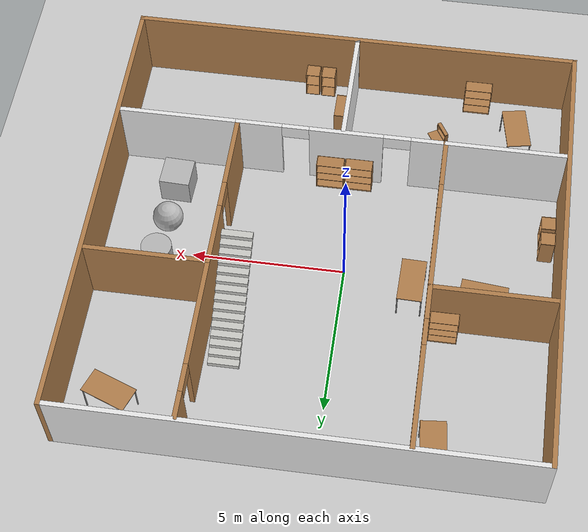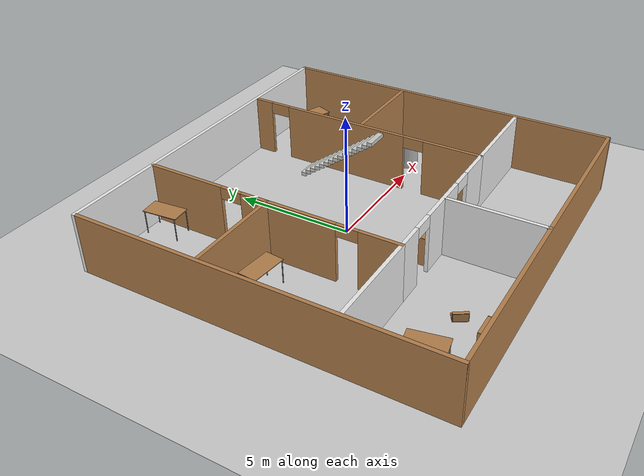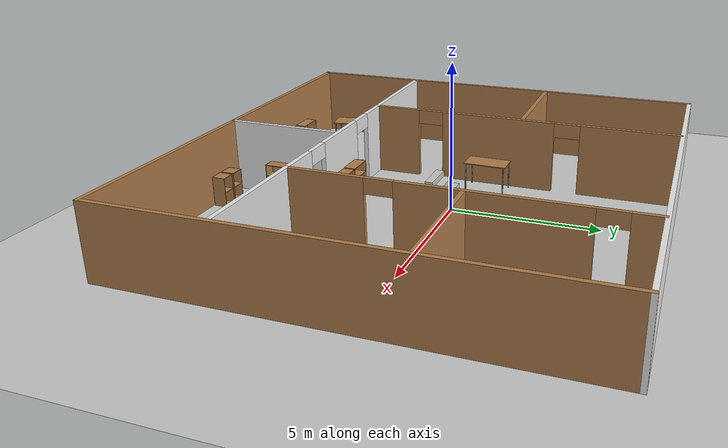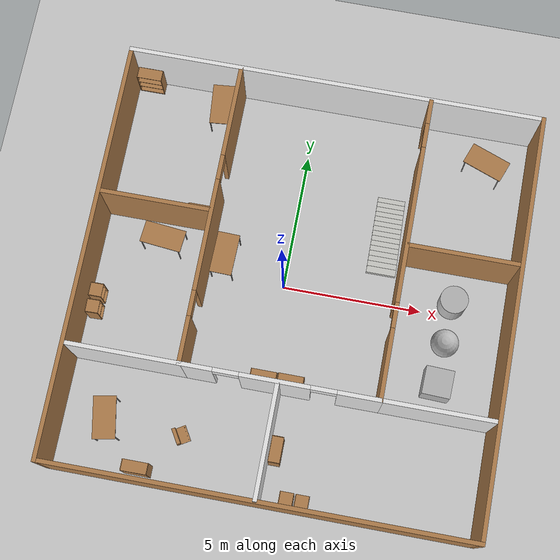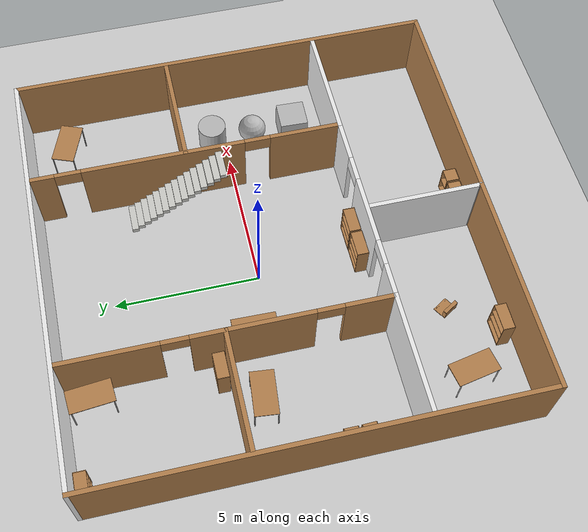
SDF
<sdf version="1.6">
 <world name="default">
  <light name="sun" type="directional">
   <pose>0 0 10 0 -0 0</pose>
   <diffuse>0.8 0.8 0.8 1</diffuse>
   <specular>0.2 0.2 0.2 1</specular>
   <attenuation>
    <range>1000</range>
    <constant>0.9</constant>
    <linear>0.01</linear>
    <quadratic>0.001</quadratic>
   </attenuation>
   <direction>-0.5 0.1 -0.9</direction>
   <spot><inner_angle>0</inner_angle><outer_angle>0</outer_angle><falloff>0</falloff></spot>
  </light>
  <model name="ground_plane">
   <static>1</static>
   <link name="link">
    <collision name="collision">
     <geometry><plane><normal>0 0 1</normal><size>100 100</size></plane></geometry>
     <surface>
      <contact><collide_bitmask>65535</collide_bitmask></contact>
      <friction><ode><mu>100</mu><mu2>50</mu2></ode></friction>
     </surface>
    </collision>
    <visual name="visual">
     <cast_shadows>0</cast_shadows>
     <geometry><plane><normal>0 0 1</normal><size>100 100</size></plane></geometry>
     <material>
      <script><uri>file://media/materials/scripts/gazebo.material</uri><name>Gazebo/Grey</name></script>
     </material>
    </visual>
   </link>
  </model>
  <gravity>0 0 -9.8</gravity>
  <magnetic_field>6e-06 2.3e-05 -4.2e-05</magnetic_field>
  <atmosphere type="adiabatic"/>
  <physics name="default_physics" default="0" type="ode">
   <max_step_size>0.001</max_step_size>
   <real_time_factor>1</real_time_factor>
   <real_time_update_rate>1000</real_time_update_rate>
  </physics>
  <scene><ambient>0.4 0.4 0.4 1</ambient><background>0.7 0.7 0.7 1</background><shadows>1</shadows></scene>
  <spherical_coordinates>
   <surface_model>EARTH_WGS84</surface_model>
   <latitude_deg>0</latitude_deg>
   <longitude_deg>0</longitude_deg>
   <elevation>0</elevation>
   <heading_deg>0</heading_deg>
  </spherical_coordinates>
  <model name="table">
   <static>1</static>
   <link name="link">
    <collision name="surface">
     <pose>0 0 1 0 -0 0</pose>
     <geometry><box><size>1.5 0.8 0.03</size></box></geometry>
     <surface><friction><ode><mu>0.6</mu><mu2>0.6</mu2></ode></friction></surface>
    </collision>
    <visual name="visual1">
     <pose>0 0 1 0 -0 0</pose>
     <geometry><box><size>1.5 0.8 0.03</size></box></geometry>
     <material>
      <script><uri>file://media/materials/scripts/gazebo.material</uri><name>Gazebo/Wood</name></script>
     </material>
    </visual>
    <collision name="front_left_leg">
     <pose>0.68 0.38 0.5 0 -0 0</pose>
     <geometry><cylinder><radius>0.02</radius><length>1</length></cylinder></geometry>
    </collision>
    <visual name="front_left_leg">
     <pose>0.68 0.38 0.5 0 -0 0</pose>
     <geometry><cylinder><radius>0.02</radius><length>1</length></cylinder></geometry>
     <material>
      <script><uri>file://media/materials/scripts/gazebo.material</uri><name>Gazebo/Grey</name></script>
     </material>
    </visual>
    <collision name="front_right_leg">
     <pose>0.68 -0.38 0.5 0 -0 0</pose>
     <geometry><cylinder><radius>0.02</radius><length>1</length></cylinder></geometry>
    </collision>
    <visual name="front_right_leg">
     <pose>0.68 -0.38 0.5 0 -0 0</pose>
     <geometry><cylinder><radius>0.02</radius><length>1</length></cylinder></geometry>
     <material>
      <script><uri>file://media/materials/scripts/gazebo.material</uri><name>Gazebo/Grey</name></script>
     </material>
    </visual>
    <collision name="back_right_leg">
     <pose>-0.68 -0.38 0.5 0 -0 0</pose>
     <geometry><cylinder><radius>0.02</radius><length>1</length></cylinder></geometry>
    </collision>
    <visual name="back_right_leg">
     <pose>-0.68 -0.38 0.5 0 -0 0</pose>
     <geometry><cylinder><radius>0.02</radius><length>1</length></cylinder></geometry>
     <material>
      <script><uri>file://media/materials/scripts/gazebo.material</uri><name>Gazebo/Grey</name></script>
     </material>
    </visual>
    <collision name="back_left_leg">
     <pose>-0.68 0.38 0.5 0 -0 0</pose>
     <geometry><cylinder><radius>0.02</radius><length>1</length></cylinder></geometry>
    </collision>
    <visual name="back_left_leg">
     <pose>-0.68 0.38 0.5 0 -0 0</pose>
     <geometry><cylinder><radius>0.02</radius><length>1</length></cylinder></geometry>
     <material>
      <script><uri>file://media/materials/scripts/gazebo.material</uri><name>Gazebo/Grey</name></script>
     </material>
    </visual>
   </link>
   <pose>-4.51795 0.830901 0 0 0 -0.09973</pose>
  </model>
  <model name="table_0">
   <static>1</static>
   <link name="link">
    <collision name="surface">
     <pose>0 0 1 0 -0 0</pose>
     <geometry><box><size>1.5 0.8 0.03</size></box></geometry>
     <surface><friction><ode><mu>0.6</mu><mu2>0.6</mu2></ode></friction></surface>
    </collision>
    <visual name="visual1">
     <pose>0 0 1 0 -0 0</pose>
     <geometry><box><size>1.5 0.8 0.03</size></box></geometry>
     <material>
      <script><uri>file://media/materials/scripts/gazebo.material</uri><name>Gazebo/Wood</name></script>
     </material>
    </visual>
    <collision name="front_left_leg">
     <pose>0.68 0.38 0.5 0 -0 0</pose>
     <geometry><cylinder><radius>0.02</radius><length>1</length></cylinder></geometry>
    </collision>
    <visual name="front_left_leg">
     <pose>0.68 0.38 0.5 0 -0 0</pose>
     <geometry><cylinder><radius>0.02</radius><length>1</length></cylinder></geometry>
     <material>
      <script><uri>file://media/materials/scripts/gazebo.material</uri><name>Gazebo/Grey</name></script>
     </material>
    </visual>
    <collision name="front_right_leg">
     <pose>0.68 -0.38 0.5 0 -0 0</pose>
     <geometry><cylinder><radius>0.02</radius><length>1</length></cylinder></geometry>
    </collision>
    <visual name="front_right_leg">
     <pose>0.68 -0.38 0.5 0 -0 0</pose>
     <geometry><cylinder><radius>0.02</radius><length>1</length></cylinder></geometry>
     <material>
      <script><uri>file://media/materials/scripts/gazebo.material</uri><name>Gazebo/Grey</name></script>
     </material>
    </visual>
    <collision name="back_right_leg">
     <pose>-0.68 -0.38 0.5 0 -0 0</pose>
     <geometry><cylinder><radius>0.02</radius><length>1</length></cylinder></geometry>
    </collision>
    <visual name="back_right_leg">
     <pose>-0.68 -0.38 0.5 0 -0 0</pose>
     <geometry><cylinder><radius>0.02</radius><length>1</length></cylinder></geometry>
     <material>
      <script><uri>file://media/materials/scripts/gazebo.material</uri><name>Gazebo/Grey</name></script>
     </material>
    </visual>
    <collision name="back_left_leg">
     <pose>-0.68 0.38 0.5 0 -0 0</pose>
     <geometry><cylinder><radius>0.02</radius><length>1</length></cylinder></geometry>
    </collision>
    <visual name="back_left_leg">
     <pose>-0.68 0.38 0.5 0 -0 0</pose>
     <geometry><cylinder><radius>0.02</radius><length>1</length></cylinder></geometry>
     <material>
      <script><uri>file://media/materials/scripts/gazebo.material</uri><name>Gazebo/Grey</name></script>
     </material>
    </visual>
   </link>
   <pose>-2.23339 0.613109 0 0 0 -1.59289</pose>
  </model>
  <model name="table_1">
   <static>1</static>
   <link name="link">
    <collision name="surface">
     <pose>0 0 1 0 -0 0</pose>
     <geometry><box><size>1.5 0.8 0.03</size></box></geometry>
     <surface><friction><ode><mu>0.6</mu><mu2>0.6</mu2></ode></friction></surface>
    </collision>
    <visual name="visual1">
     <pose>0 0 1 0 -0 0</pose>
     <geometry><box><size>1.5 0.8 0.03</size></box></geometry>
     <material>
      <script><uri>file://media/materials/scripts/gazebo.material</uri><name>Gazebo/Wood</name></script>
     </material>
    </visual>
    <collision name="front_left_leg">
     <pose>0.68 0.38 0.5 0 -0 0</pose>
     <geometry><cylinder><radius>0.02</radius><length>1</length></cylinder></geometry>
    </collision>
    <visual name="front_left_leg">
     <pose>0.68 0.38 0.5 0 -0 0</pose>
     <geometry><cylinder><radius>0.02</radius><length>1</length></cylinder></geometry>
     <material>
      <script><uri>file://media/materials/scripts/gazebo.material</uri><name>Gazebo/Grey</name></script>
     </material>
    </visual>
    <collision name="front_right_leg">
     <pose>0.68 -0.38 0.5 0 -0 0</pose>
     <geometry><cylinder><radius>0.02</radius><length>1</length></cylinder></geometry>
    </collision>
    <visual name="front_right_leg">
     <pose>0.68 -0.38 0.5 0 -0 0</pose>
     <geometry><cylinder><radius>0.02</radius><length>1</length></cylinder></geometry>
     <material>
      <script><uri>file://media/materials/scripts/gazebo.material</uri><name>Gazebo/Grey</name></script>
     </material>
    </visual>
    <collision name="back_right_leg">
     <pose>-0.68 -0.38 0.5 0 -0 0</pose>
     <geometry><cylinder><radius>0.02</radius><length>1</length></cylinder></geometry>
    </collision>
    <visual name="back_right_leg">
     <pose>-0.68 -0.38 0.5 0 -0 0</pose>
     <geometry><cylinder><radius>0.02</radius><length>1</length></cylinder></geometry>
     <material>
      <script><uri>file://media/materials/scripts/gazebo.material</uri><name>Gazebo/Grey</name></script>
     </material>
    </visual>
    <collision name="back_left_leg">
     <pose>-0.68 0.38 0.5 0 -0 0</pose>
     <geometry><cylinder><radius>0.02</radius><length>1</length></cylinder></geometry>
    </collision>
    <visual name="back_left_leg">
     <pose>-0.68 0.38 0.5 0 -0 0</pose>
     <geometry><cylinder><radius>0.02</radius><length>1</length></cylinder></geometry>
     <material>
      <script><uri>file://media/materials/scripts/gazebo.material</uri><name>Gazebo/Grey</name></script>
     </material>
    </visual>
   </link>
   <pose>-3.43138 6.15377 0 0 -0 1.6649</pose>
  </model>
  <model name="table_2">
   <static>1</static>
   <link name="link">
    <collision name="surface">
     <pose>0 0 1 0 -0 0</pose>
     <geometry><box><size>1.5 0.8 0.03</size></box></geometry>
     <surface><friction><ode><mu>0.6</mu><mu2>0.6</mu2></ode></friction></surface>
    </collision>
    <visual name="visual1">
     <pose>0 0 1 0 -0 0</pose>
     <geometry><box><size>1.5 0.8 0.03</size></box></geometry>
     <material>
      <script><uri>file://media/materials/scripts/gazebo.material</uri><name>Gazebo/Wood</name></script>
     </material>
    </visual>
    <collision name="front_left_leg">
     <pose>0.68 0.38 0.5 0 -0 0</pose>
     <geometry><cylinder><radius>0.02</radius><length>1</length></cylinder></geometry>
    </collision>
    <visual name="front_left_leg">
     <pose>0.68 0.38 0.5 0 -0 0</pose>
     <geometry><cylinder><radius>0.02</radius><length>1</length></cylinder></geometry>
     <material>
      <script><uri>file://media/materials/scripts/gazebo.material</uri><name>Gazebo/Grey</name></script>
     </material>
    </visual>
    <collision name="front_right_leg">
     <pose>0.68 -0.38 0.5 0 -0 0</pose>
     <geometry><cylinder><radius>0.02</radius><length>1</length></cylinder></geometry>
    </collision>
    <visual name="front_right_leg">
     <pose>0.68 -0.38 0.5 0 -0 0</pose>
     <geometry><cylinder><radius>0.02</radius><length>1</length></cylinder></geometry>
     <material>
      <script><uri>file://media/materials/scripts/gazebo.material</uri><name>Gazebo/Grey</name></script>
     </material>
    </visual>
    <collision name="back_right_leg">
     <pose>-0.68 -0.38 0.5 0 -0 0</pose>
     <geometry><cylinder><radius>0.02</radius><length>1</length></cylinder></geometry>
    </collision>
    <visual name="back_right_leg">
     <pose>-0.68 -0.38 0.5 0 -0 0</pose>
     <geometry><cylinder><radius>0.02</radius><length>1</length></cylinder></geometry>
     <material>
      <script><uri>file://media/materials/scripts/gazebo.material</uri><name>Gazebo/Grey</name></script>
     </material>
    </visual>
    <collision name="back_left_leg">
     <pose>-0.68 0.38 0.5 0 -0 0</pose>
     <geometry><cylinder><radius>0.02</radius><length>1</length></cylinder></geometry>
    </collision>
    <visual name="back_left_leg">
     <pose>-0.68 0.38 0.5 0 -0 0</pose>
     <geometry><cylinder><radius>0.02</radius><length>1</length></cylinder></geometry>
     <material>
      <script><uri>file://media/materials/scripts/gazebo.material</uri><name>Gazebo/Grey</name></script>
     </material>
    </visual>
   </link>
   <pose>6.43262 5.68773 0 0 0 -0.358912</pose>
  </model>
  <model name="table_3">
   <static>1</static>
   <link name="link">
    <collision name="surface">
     <pose>0 0 1 0 -0 0</pose>
     <geometry><box><size>1.5 0.8 0.03</size></box></geometry>
     <surface><friction><ode><mu>0.6</mu><mu2>0.6</mu2></ode></friction></surface>
    </collision>
    <visual name="visual1">
     <pose>0 0 1 0 -0 0</pose>
     <geometry><box><size>1.5 0.8 0.03</size></box></geometry>
     <material>
      <script><uri>file://media/materials/scripts/gazebo.material</uri><name>Gazebo/Wood</name></script>
     </material>
    </visual>
    <collision name="front_left_leg">
     <pose>0.68 0.38 0.5 0 -0 0</pose>
     <geometry><cylinder><radius>0.02</radius><length>1</length></cylinder></geometry>
    </collision>
    <visual name="front_left_leg">
     <pose>0.68 0.38 0.5 0 -0 0</pose>
     <geometry><cylinder><radius>0.02</radius><length>1</length></cylinder></geometry>
     <material>
      <script><uri>file://media/materials/scripts/gazebo.material</uri><name>Gazebo/Grey</name></script>
     </material>
    </visual>
    <collision name="front_right_leg">
     <pose>0.68 -0.38 0.5 0 -0 0</pose>
     <geometry><cylinder><radius>0.02</radius><length>1</length></cylinder></geometry>
    </collision>
    <visual name="front_right_leg">
     <pose>0.68 -0.38 0.5 0 -0 0</pose>
     <geometry><cylinder><radius>0.02</radius><length>1</length></cylinder></geometry>
     <material>
      <script><uri>file://media/materials/scripts/gazebo.material</uri><name>Gazebo/Grey</name></script>
     </material>
    </visual>
    <collision name="back_right_leg">
     <pose>-0.68 -0.38 0.5 0 -0 0</pose>
     <geometry><cylinder><radius>0.02</radius><length>1</length></cylinder></geometry>
    </collision>
    <visual name="back_right_leg">
     <pose>-0.68 -0.38 0.5 0 -0 0</pose>
     <geometry><cylinder><radius>0.02</radius><length>1</length></cylinder></geometry>
     <material>
      <script><uri>file://media/materials/scripts/gazebo.material</uri><name>Gazebo/Grey</name></script>
     </material>
    </visual>
    <collision name="back_left_leg">
     <pose>-0.68 0.38 0.5 0 -0 0</pose>
     <geometry><cylinder><radius>0.02</radius><length>1</length></cylinder></geometry>
    </collision>
    <visual name="back_left_leg">
     <pose>-0.68 0.38 0.5 0 -0 0</pose>
     <geometry><cylinder><radius>0.02</radius><length>1</length></cylinder></geometry>
     <material>
      <script><uri>file://media/materials/scripts/gazebo.material</uri><name>Gazebo/Grey</name></script>
     </material>
    </visual>
   </link>
   <pose>-5.14548 -5.86576 0 0 0 -1.38337</pose>
  </model>
  <model name="textured_shapes">
   <pose>5.99523 -1.07285 0.5 0 -0 -0.035266</pose>
   <link name="box">
    <pose>0 -1.5 0 0 -0 0</pose>
    <collision name="collision"><geometry><box><size>1 1 1</size></box></geometry></collision>
    <visual name="visual">
     <geometry><box><size>1 1 1</size></box></geometry>
     <material>
      <script>
       <uri>model://textured_shapes/materials/scripts</uri>
       <uri>model://textured_shapes/materials/textures</uri>
       <name>TexturedShape/Squares</name>
      </script>
     </material>
    </visual>
    <inertial>
     <inertia><ixx>1</ixx><ixy>0</ixy><ixz>0</ixz><iyy>1</iyy><iyz>0</iyz><izz>1</izz></inertia>
     <mass>1</mass>
    </inertial>
   </link>
   <link name="sphere">
    <collision name="collision"><geometry><sphere><radius>0.5</radius></sphere></geometry></collision>
    <visual name="visual">
     <geometry><sphere><radius>0.5</radius></sphere></geometry>
     <material>
      <script>
       <uri>model://textured_shapes/materials/scripts</uri>
       <uri>model://textured_shapes/materials/textures</uri>
       <name>TexturedShape/Squares</name>
      </script>
     </material>
    </visual>
    <inertial>
     <inertia><ixx>1</ixx><ixy>0</ixy><ixz>0</ixz><iyy>1</iyy><iyz>0</iyz><izz>1</izz></inertia>
     <mass>1</mass>
    </inertial>
   </link>
   <link name="cylinder">
    <pose>0 1.5 0 0 -0 0</pose>
    <collision name="collision">
     <geometry><cylinder><radius>0.5</radius><length>1</length></cylinder></geometry>
    </collision>
    <visual name="visual">
     <geometry><cylinder><radius>0.5</radius><length>1</length></cylinder></geometry>
     <material>
      <script>
       <uri>model://textured_shapes/materials/scripts</uri>
       <uri>model://textured_shapes/materials/textures</uri>
       <name>TexturedShape/Squares</name>
      </script>
     </material>
    </visual>
    <inertial>
     <inertia><ixx>1</ixx><ixy>0</ixy><ixz>0</ixz><iyy>1</iyy><iyz>0</iyz><izz>1</izz></inertia>
     <mass>1</mass>
    </inertial>
   </link>
  </model>
  <light name="user_point_light_0" type="point">
   <pose>0.331076 1.16128 1 0 -0 0</pose>
   <diffuse>0.5 0.5 0.5 1</diffuse>
   <specular>0.1 0.1 0.1 1</specular>
   <attenuation>
    <range>20</range>
    <constant>0.5</constant>
    <linear>0.4</linear>
    <quadratic>0.001</quadratic>
   </attenuation>
   <cast_shadows>0</cast_shadows>
   <direction>0 0 -1</direction>
   <spot><inner_angle>0</inner_angle><outer_angle>0</outer_angle><falloff>0</falloff></spot>
  </light>
  <model name="bookshelf">
   <static>1</static>
   <link name="link">
    <inertial><mass>1</mass></inertial>
    <collision name="back">
     <pose>0 0.005 0.6 0 -0 0</pose>
     <geometry><box><size>0.9 0.01 1.2</size></box></geometry>
    </collision>
    <visual name="visual1">
     <pose>0 0.005 0.6 0 -0 0</pose>
     <geometry><box><size>0.9 0.01 1.2</size></box></geometry>
     <material>
      <script><uri>file://media/materials/scripts/gazebo.material</uri><name>Gazebo/Wood</name></script>
     </material>
    </visual>
    <collision name="left_side">
     <pose>0.45 -0.195 0.6 0 -0 0</pose>
     <geometry><box><size>0.02 0.4 1.2</size></box></geometry>
    </collision>
    <visual name="visual2">
     <pose>0.45 -0.195 0.6 0 -0 0</pose>
     <geometry><box><size>0.02 0.4 1.2</size></box></geometry>
     <material>
      <script><uri>file://media/materials/scripts/gazebo.material</uri><name>Gazebo/Wood</name></script>
     </material>
    </visual>
    <collision name="right_side">
     <pose>-0.45 -0.195 0.6 0 -0 0</pose>
     <geometry><box><size>0.02 0.4 1.2</size></box></geometry>
    </collision>
    <visual name="visual3">
     <pose>-0.45 -0.195 0.6 0 -0 0</pose>
     <geometry><box><size>0.02 0.4 1.2</size></box></geometry>
     <material>
      <script><uri>file://media/materials/scripts/gazebo.material</uri><name>Gazebo/Wood</name></script>
     </material>
    </visual>
    <collision name="bottom">
     <pose>0 -0.195 0.03 0 -0 0</pose>
     <geometry><box><size>0.88 0.4 0.06</size></box></geometry>
    </collision>
    <visual name="visual4">
     <pose>0 -0.195 0.03 0 -0 0</pose>
     <geometry><box><size>0.88 0.4 0.06</size></box></geometry>
     <material>
      <script><uri>file://media/materials/scripts/gazebo.material</uri><name>Gazebo/Wood</name></script>
     </material>
    </visual>
    <collision name="top">
     <pose>0 -0.195 1.19 0 -0 0</pose>
     <geometry><box><size>0.88 0.4 0.02</size></box></geometry>
    </collision>
    <visual name="visual5">
     <pose>0 -0.195 1.19 0 -0 0</pose>
     <geometry><box><size>0.88 0.4 0.02</size></box></geometry>
     <material>
      <script><uri>file://media/materials/scripts/gazebo.material</uri><name>Gazebo/Wood</name></script>
     </material>
    </visual>
    <collision name="low_shelf">
     <pose>0 -0.195 0.43 0 -0 0</pose>
     <geometry><box><size>0.88 0.4 0.02</size></box></geometry>
    </collision>
    <visual name="visual6">
     <pose>0 -0.195 0.43 0 -0 0</pose>
     <geometry><box><size>0.88 0.4 0.02</size></box></geometry>
     <material>
      <script><uri>file://media/materials/scripts/gazebo.material</uri><name>Gazebo/Wood</name></script>
     </material>
    </visual>
    <collision name="high_shelf">
     <pose>0 -0.195 0.8 0 -0 0</pose>
     <geometry><box><size>0.88 0.4 0.02</size></box></geometry>
    </collision>
    <visual name="visual7">
     <pose>0 -0.195 0.8 0 -0 0</pose>
     <geometry><box><size>0.88 0.4 0.02</size></box></geometry>
     <material>
      <script><uri>file://media/materials/scripts/gazebo.material</uri><name>Gazebo/Wood</name></script>
     </material>
    </visual>
   </link>
   <pose>-0.042308 -3.68874 0 0 -0 3.14159</pose>
  </model>
  <model name="bookshelf_clone">
   <static>1</static>
   <link name="link">
    <inertial><mass>1</mass></inertial>
    <collision name="back">
     <pose>0 0.005 0.6 0 -0 0</pose>
     <geometry><box><size>0.9 0.01 1.2</size></box></geometry>
    </collision>
    <visual name="visual1">
     <pose>0 0.005 0.6 0 -0 0</pose>
     <geometry><box><size>0.9 0.01 1.2</size></box></geometry>
     <material>
      <script><uri>file://media/materials/scripts/gazebo.material</uri><name>Gazebo/Wood</name></script>
     </material>
    </visual>
    <collision name="left_side">
     <pose>0.45 -0.195 0.6 0 -0 0</pose>
     <geometry><box><size>0.02 0.4 1.2</size></box></geometry>
    </collision>
    <visual name="visual2">
     <pose>0.45 -0.195 0.6 0 -0 0</pose>
     <geometry><box><size>0.02 0.4 1.2</size></box></geometry>
     <material>
      <script><uri>file://media/materials/scripts/gazebo.material</uri><name>Gazebo/Wood</name></script>
     </material>
    </visual>
    <collision name="right_side">
     <pose>-0.45 -0.195 0.6 0 -0 0</pose>
     <geometry><box><size>0.02 0.4 1.2</size></box></geometry>
    </collision>
    <visual name="visual3">
     <pose>-0.45 -0.195 0.6 0 -0 0</pose>
     <geometry><box><size>0.02 0.4 1.2</size></box></geometry>
     <material>
      <script><uri>file://media/materials/scripts/gazebo.material</uri><name>Gazebo/Wood</name></script>
     </material>
    </visual>
    <collision name="bottom">
     <pose>0 -0.195 0.03 0 -0 0</pose>
     <geometry><box><size>0.88 0.4 0.06</size></box></geometry>
    </collision>
    <visual name="visual4">
     <pose>0 -0.195 0.03 0 -0 0</pose>
     <geometry><box><size>0.88 0.4 0.06</size></box></geometry>
     <material>
      <script><uri>file://media/materials/scripts/gazebo.material</uri><name>Gazebo/Wood</name></script>
     </material>
    </visual>
    <collision name="top">
     <pose>0 -0.195 1.19 0 -0 0</pose>
     <geometry><box><size>0.88 0.4 0.02</size></box></geometry>
    </collision>
    <visual name="visual5">
     <pose>0 -0.195 1.19 0 -0 0</pose>
     <geometry><box><size>0.88 0.4 0.02</size></box></geometry>
     <material>
      <script><uri>file://media/materials/scripts/gazebo.material</uri><name>Gazebo/Wood</name></script>
     </material>
    </visual>
    <collision name="low_shelf">
     <pose>0 -0.195 0.43 0 -0 0</pose>
     <geometry><box><size>0.88 0.4 0.02</size></box></geometry>
    </collision>
    <visual name="visual6">
     <pose>0 -0.195 0.43 0 -0 0</pose>
     <geometry><box><size>0.88 0.4 0.02</size></box></geometry>
     <material>
      <script><uri>file://media/materials/scripts/gazebo.material</uri><name>Gazebo/Wood</name></script>
     </material>
    </visual>
    <collision name="high_shelf">
     <pose>0 -0.195 0.8 0 -0 0</pose>
     <geometry><box><size>0.88 0.4 0.02</size></box></geometry>
    </collision>
    <visual name="visual7">
     <pose>0 -0.195 0.8 0 -0 0</pose>
     <geometry><box><size>0.88 0.4 0.02</size></box></geometry>
     <material>
      <script><uri>file://media/materials/scripts/gazebo.material</uri><name>Gazebo/Wood</name></script>
     </material>
    </visual>
   </link>
   <pose>0.908578 -3.67779 0 0 -0 3.14159</pose>
  </model>
  <model name="cabinet_clone">
   <static>1</static>
   <link name="cabinet_bottom_plate">
    <inertial>
     <pose>0 0 -1 0 -0 0</pose>
     <inertia><ixx>2.05</ixx><ixy>0</ixy><ixz>0</ixz><iyy>2.05</iyy><iyz>0</iyz><izz>2.05</izz></inertia>
     <mass>25</mass>
    </inertial>
    <collision name="cabinet_bottom_plate_geom">
     <pose>0 0 0.01 0 -0 0</pose>
     <geometry><box><size>0.45 0.45 0.02</size></box></geometry>
    </collision>
    <visual name="cabinet_bottom_plate_geom_visual">
     <pose>0 0 0.01 0 -0 0</pose>
     <geometry><box><size>0.45 0.45 0.02</size></box></geometry>
     <material>
      <script><uri>file://media/materials/scripts/gazebo.material</uri><name>Gazebo/Wood</name></script>
     </material>
    </visual>
    <collision name="cabinet_bottom_plate_geom_cabinet_back_plate">
     <pose>0.235 0 0.51 0 -0 0</pose>
     <geometry><box><size>0.02 0.45 1.02</size></box></geometry>
    </collision>
    <visual name="cabinet_bottom_plate_geom_cabinet_back_plate_visual">
     <pose>0.235 0 0.51 0 -0 0</pose>
     <geometry><box><size>0.02 0.45 1.02</size></box></geometry>
     <material>
      <script><uri>file://media/materials/scripts/gazebo.material</uri><name>Gazebo/Wood</name></script>
     </material>
    </visual>
    <collision name="cabinet_bottom_plate_geom_cabinet_left_plate">
     <pose>0 0.235 0.51 0 -0 0</pose>
     <geometry><box><size>0.45 0.02 1.02</size></box></geometry>
    </collision>
    <visual name="cabinet_bottom_plate_geom_cabinet_left_plate_visual">
     <pose>0 0.235 0.51 0 -0 0</pose>
     <geometry><box><size>0.45 0.02 1.02</size></box></geometry>
     <material>
      <script><uri>file://media/materials/scripts/gazebo.material</uri><name>Gazebo/Wood</name></script>
     </material>
    </visual>
    <collision name="cabinet_bottom_plate_geom_cabinet_middle_plate">
     <pose>0 0 0.51 0 -0 0</pose>
     <geometry><box><size>0.45 0.45 0.02</size></box></geometry>
    </collision>
    <visual name="cabinet_bottom_plate_geom_cabinet_middle_plate_visual">
     <pose>0 0 0.51 0 -0 0</pose>
     <geometry><box><size>0.45 0.45 0.02</size></box></geometry>
     <material>
      <script><uri>file://media/materials/scripts/gazebo.material</uri><name>Gazebo/Wood</name></script>
     </material>
    </visual>
    <collision name="cabinet_bottom_plate_geom_cabinet_right_plate">
     <pose>0 -0.235 0.51 0 -0 0</pose>
     <geometry><box><size>0.45 0.02 1.02</size></box></geometry>
    </collision>
    <visual name="cabinet_bottom_plate_geom_cabinet_right_plate_visual">
     <pose>0 -0.235 0.51 0 -0 0</pose>
     <geometry><box><size>0.45 0.02 1.02</size></box></geometry>
     <material>
      <script><uri>file://media/materials/scripts/gazebo.material</uri><name>Gazebo/Wood</name></script>
     </material>
    </visual>
    <collision name="cabinet_bottom_plate_geom_cabinet_top_plate">
     <pose>0 0 1.01 0 -0 0</pose>
     <geometry><box><size>0.45 0.45 0.02</size></box></geometry>
    </collision>
    <visual name="cabinet_bottom_plate_geom_cabinet_top_plate_visual">
     <pose>0 0 1.01 0 -0 0</pose>
     <geometry><box><size>0.45 0.45 0.02</size></box></geometry>
     <material>
      <script><uri>file://media/materials/scripts/gazebo.material</uri><name>Gazebo/Wood</name></script>
     </material>
    </visual>
   </link>
   <pose>1.49574 -7.4413 0 0 0 -1.5708</pose>
  </model>
  <model name="cabinet_clone_0">
   <static>1</static>
   <link name="cabinet_bottom_plate">
    <inertial>
     <pose>0 0 -1 0 -0 0</pose>
     <inertia><ixx>2.05</ixx><ixy>0</ixy><ixz>0</ixz><iyy>2.05</iyy><iyz>0</iyz><izz>2.05</izz></inertia>
     <mass>25</mass>
    </inertial>
    <collision name="cabinet_bottom_plate_geom">
     <pose>0 0 0.01 0 -0 0</pose>
     <geometry><box><size>0.45 0.45 0.02</size></box></geometry>
    </collision>
    <visual name="cabinet_bottom_plate_geom_visual">
     <pose>0 0 0.01 0 -0 0</pose>
     <geometry><box><size>0.45 0.45 0.02</size></box></geometry>
     <material>
      <script><uri>file://media/materials/scripts/gazebo.material</uri><name>Gazebo/Wood</name></script>
     </material>
    </visual>
    <collision name="cabinet_bottom_plate_geom_cabinet_back_plate">
     <pose>0.235 0 0.51 0 -0 0</pose>
     <geometry><box><size>0.02 0.45 1.02</size></box></geometry>
    </collision>
    <visual name="cabinet_bottom_plate_geom_cabinet_back_plate_visual">
     <pose>0.235 0 0.51 0 -0 0</pose>
     <geometry><box><size>0.02 0.45 1.02</size></box></geometry>
     <material>
      <script><uri>file://media/materials/scripts/gazebo.material</uri><name>Gazebo/Wood</name></script>
     </material>
    </visual>
    <collision name="cabinet_bottom_plate_geom_cabinet_left_plate">
     <pose>0 0.235 0.51 0 -0 0</pose>
     <geometry><box><size>0.45 0.02 1.02</size></box></geometry>
    </collision>
    <visual name="cabinet_bottom_plate_geom_cabinet_left_plate_visual">
     <pose>0 0.235 0.51 0 -0 0</pose>
     <geometry><box><size>0.45 0.02 1.02</size></box></geometry>
     <material>
      <script><uri>file://media/materials/scripts/gazebo.material</uri><name>Gazebo/Wood</name></script>
     </material>
    </visual>
    <collision name="cabinet_bottom_plate_geom_cabinet_middle_plate">
     <pose>0 0 0.51 0 -0 0</pose>
     <geometry><box><size>0.45 0.45 0.02</size></box></geometry>
    </collision>
    <visual name="cabinet_bottom_plate_geom_cabinet_middle_plate_visual">
     <pose>0 0 0.51 0 -0 0</pose>
     <geometry><box><size>0.45 0.45 0.02</size></box></geometry>
     <material>
      <script><uri>file://media/materials/scripts/gazebo.material</uri><name>Gazebo/Wood</name></script>
     </material>
    </visual>
    <collision name="cabinet_bottom_plate_geom_cabinet_right_plate">
     <pose>0 -0.235 0.51 0 -0 0</pose>
     <geometry><box><size>0.45 0.02 1.02</size></box></geometry>
    </collision>
    <visual name="cabinet_bottom_plate_geom_cabinet_right_plate_visual">
     <pose>0 -0.235 0.51 0 -0 0</pose>
     <geometry><box><size>0.45 0.02 1.02</size></box></geometry>
     <material>
      <script><uri>file://media/materials/scripts/gazebo.material</uri><name>Gazebo/Wood</name></script>
     </material>
    </visual>
    <collision name="cabinet_bottom_plate_geom_cabinet_top_plate">
     <pose>0 0 1.01 0 -0 0</pose>
     <geometry><box><size>0.45 0.45 0.02</size></box></geometry>
    </collision>
    <visual name="cabinet_bottom_plate_geom_cabinet_top_plate_visual">
     <pose>0 0 1.01 0 -0 0</pose>
     <geometry><box><size>0.45 0.45 0.02</size></box></geometry>
     <material>
      <script><uri>file://media/materials/scripts/gazebo.material</uri><name>Gazebo/Wood</name></script>
     </material>
    </visual>
   </link>
   <pose>2.03504 -7.44814 0 0 0 -1.5708</pose>
  </model>
  <model name="bookshelf_clone_clone">
   <static>1</static>
   <link name="link">
    <inertial><mass>1</mass></inertial>
    <collision name="back">
     <pose>0 0.005 0.6 0 -0 0</pose>
     <geometry><box><size>0.9 0.01 1.2</size></box></geometry>
    </collision>
    <visual name="visual1">
     <pose>0 0.005 0.6 0 -0 0</pose>
     <geometry><box><size>0.9 0.01 1.2</size></box></geometry>
     <material>
      <script><uri>file://media/materials/scripts/gazebo.material</uri><name>Gazebo/Wood</name></script>
     </material>
    </visual>
    <collision name="left_side">
     <pose>0.45 -0.195 0.6 0 -0 0</pose>
     <geometry><box><size>0.02 0.4 1.2</size></box></geometry>
    </collision>
    <visual name="visual2">
     <pose>0.45 -0.195 0.6 0 -0 0</pose>
     <geometry><box><size>0.02 0.4 1.2</size></box></geometry>
     <material>
      <script><uri>file://media/materials/scripts/gazebo.material</uri><name>Gazebo/Wood</name></script>
     </material>
    </visual>
    <collision name="right_side">
     <pose>-0.45 -0.195 0.6 0 -0 0</pose>
     <geometry><box><size>0.02 0.4 1.2</size></box></geometry>
    </collision>
    <visual name="visual3">
     <pose>-0.45 -0.195 0.6 0 -0 0</pose>
     <geometry><box><size>0.02 0.4 1.2</size></box></geometry>
     <material>
      <script><uri>file://media/materials/scripts/gazebo.material</uri><name>Gazebo/Wood</name></script>
     </material>
    </visual>
    <collision name="bottom">
     <pose>0 -0.195 0.03 0 -0 0</pose>
     <geometry><box><size>0.88 0.4 0.06</size></box></geometry>
    </collision>
    <visual name="visual4">
     <pose>0 -0.195 0.03 0 -0 0</pose>
     <geometry><box><size>0.88 0.4 0.06</size></box></geometry>
     <material>
      <script><uri>file://media/materials/scripts/gazebo.material</uri><name>Gazebo/Wood</name></script>
     </material>
    </visual>
    <collision name="top">
     <pose>0 -0.195 1.19 0 -0 0</pose>
     <geometry><box><size>0.88 0.4 0.02</size></box></geometry>
    </collision>
    <visual name="visual5">
     <pose>0 -0.195 1.19 0 -0 0</pose>
     <geometry><box><size>0.88 0.4 0.02</size></box></geometry>
     <material>
      <script><uri>file://media/materials/scripts/gazebo.material</uri><name>Gazebo/Wood</name></script>
     </material>
    </visual>
    <collision name="low_shelf">
     <pose>0 -0.195 0.43 0 -0 0</pose>
     <geometry><box><size>0.88 0.4 0.02</size></box></geometry>
    </collision>
    <visual name="visual6">
     <pose>0 -0.195 0.43 0 -0 0</pose>
     <geometry><box><size>0.88 0.4 0.02</size></box></geometry>
     <material>
      <script><uri>file://media/materials/scripts/gazebo.material</uri><name>Gazebo/Wood</name></script>
     </material>
    </visual>
    <collision name="high_shelf">
     <pose>0 -0.195 0.8 0 -0 0</pose>
     <geometry><box><size>0.88 0.4 0.02</size></box></geometry>
    </collision>
    <visual name="visual7">
     <pose>0 -0.195 0.8 0 -0 0</pose>
     <geometry><box><size>0.88 0.4 0.02</size></box></geometry>
     <material>
      <script><uri>file://media/materials/scripts/gazebo.material</uri><name>Gazebo/Wood</name></script>
     </material>
    </visual>
   </link>
   <pose>0.663344 -5.89171 0 0 -0 1.57079</pose>
  </model>
  <model name="bookshelf_clone_0">
   <static>1</static>
   <link name="link">
    <inertial><mass>1</mass></inertial>
    <collision name="back">
     <pose>0 0.005 0.6 0 -0 0</pose>
     <geometry><box><size>0.9 0.01 1.2</size></box></geometry>
    </collision>
    <visual name="visual1">
     <pose>0 0.005 0.6 0 -0 0</pose>
     <geometry><box><size>0.9 0.01 1.2</size></box></geometry>
     <material>
      <script><uri>file://media/materials/scripts/gazebo.material</uri><name>Gazebo/Wood</name></script>
     </material>
    </visual>
    <collision name="left_side">
     <pose>0.45 -0.195 0.6 0 -0 0</pose>
     <geometry><box><size>0.02 0.4 1.2</size></box></geometry>
    </collision>
    <visual name="visual2">
     <pose>0.45 -0.195 0.6 0 -0 0</pose>
     <geometry><box><size>0.02 0.4 1.2</size></box></geometry>
     <material>
      <script><uri>file://media/materials/scripts/gazebo.material</uri><name>Gazebo/Wood</name></script>
     </material>
    </visual>
    <collision name="right_side">
     <pose>-0.45 -0.195 0.6 0 -0 0</pose>
     <geometry><box><size>0.02 0.4 1.2</size></box></geometry>
    </collision>
    <visual name="visual3">
     <pose>-0.45 -0.195 0.6 0 -0 0</pose>
     <geometry><box><size>0.02 0.4 1.2</size></box></geometry>
     <material>
      <script><uri>file://media/materials/scripts/gazebo.material</uri><name>Gazebo/Wood</name></script>
     </material>
    </visual>
    <collision name="bottom">
     <pose>0 -0.195 0.03 0 -0 0</pose>
     <geometry><box><size>0.88 0.4 0.06</size></box></geometry>
    </collision>
    <visual name="visual4">
     <pose>0 -0.195 0.03 0 -0 0</pose>
     <geometry><box><size>0.88 0.4 0.06</size></box></geometry>
     <material>
      <script><uri>file://media/materials/scripts/gazebo.material</uri><name>Gazebo/Wood</name></script>
     </material>
    </visual>
    <collision name="top">
     <pose>0 -0.195 1.19 0 -0 0</pose>
     <geometry><box><size>0.88 0.4 0.02</size></box></geometry>
    </collision>
    <visual name="visual5">
     <pose>0 -0.195 1.19 0 -0 0</pose>
     <geometry><box><size>0.88 0.4 0.02</size></box></geometry>
     <material>
      <script><uri>file://media/materials/scripts/gazebo.material</uri><name>Gazebo/Wood</name></script>
     </material>
    </visual>
    <collision name="low_shelf">
     <pose>0 -0.195 0.43 0 -0 0</pose>
     <geometry><box><size>0.88 0.4 0.02</size></box></geometry>
    </collision>
    <visual name="visual6">
     <pose>0 -0.195 0.43 0 -0 0</pose>
     <geometry><box><size>0.88 0.4 0.02</size></box></geometry>
     <material>
      <script><uri>file://media/materials/scripts/gazebo.material</uri><name>Gazebo/Wood</name></script>
     </material>
    </visual>
    <collision name="high_shelf">
     <pose>0 -0.195 0.8 0 -0 0</pose>
     <geometry><box><size>0.88 0.4 0.02</size></box></geometry>
    </collision>
    <visual name="visual7">
     <pose>0 -0.195 0.8 0 -0 0</pose>
     <geometry><box><size>0.88 0.4 0.02</size></box></geometry>
     <material>
      <script><uri>file://media/materials/scripts/gazebo.material</uri><name>Gazebo/Wood</name></script>
     </material>
    </visual>
   </link>
   <pose>-6.25447 6.96238 0 0 0 -3e-06</pose>
  </model>
  <model name="bookshelf_clone_2">
   <static>1</static>
   <link name="link">
    <inertial><mass>1</mass></inertial>
    <collision name="back">
     <pose>0 0.005 0.6 0 -0 0</pose>
     <geometry><box><size>0.9 0.01 1.2</size></box></geometry>
    </collision>
    <visual name="visual1">
     <pose>0 0.005 0.6 0 -0 0</pose>
     <geometry><box><size>0.9 0.01 1.2</size></box></geometry>
     <material>
      <script><uri>file://media/materials/scripts/gazebo.material</uri><name>Gazebo/Wood</name></script>
     </material>
    </visual>
    <collision name="left_side">
     <pose>0.45 -0.195 0.6 0 -0 0</pose>
     <geometry><box><size>0.02 0.4 1.2</size></box></geometry>
    </collision>
    <visual name="visual2">
     <pose>0.45 -0.195 0.6 0 -0 0</pose>
     <geometry><box><size>0.02 0.4 1.2</size></box></geometry>
     <material>
      <script><uri>file://media/materials/scripts/gazebo.material</uri><name>Gazebo/Wood</name></script>
     </material>
    </visual>
    <collision name="right_side">
     <pose>-0.45 -0.195 0.6 0 -0 0</pose>
     <geometry><box><size>0.02 0.4 1.2</size></box></geometry>
    </collision>
    <visual name="visual3">
     <pose>-0.45 -0.195 0.6 0 -0 0</pose>
     <geometry><box><size>0.02 0.4 1.2</size></box></geometry>
     <material>
      <script><uri>file://media/materials/scripts/gazebo.material</uri><name>Gazebo/Wood</name></script>
     </material>
    </visual>
    <collision name="bottom">
     <pose>0 -0.195 0.03 0 -0 0</pose>
     <geometry><box><size>0.88 0.4 0.06</size></box></geometry>
    </collision>
    <visual name="visual4">
     <pose>0 -0.195 0.03 0 -0 0</pose>
     <geometry><box><size>0.88 0.4 0.06</size></box></geometry>
     <material>
      <script><uri>file://media/materials/scripts/gazebo.material</uri><name>Gazebo/Wood</name></script>
     </material>
    </visual>
    <collision name="top">
     <pose>0 -0.195 1.19 0 -0 0</pose>
     <geometry><box><size>0.88 0.4 0.02</size></box></geometry>
    </collision>
    <visual name="visual5">
     <pose>0 -0.195 1.19 0 -0 0</pose>
     <geometry><box><size>0.88 0.4 0.02</size></box></geometry>
     <material>
      <script><uri>file://media/materials/scripts/gazebo.material</uri><name>Gazebo/Wood</name></script>
     </material>
    </visual>
    <collision name="low_shelf">
     <pose>0 -0.195 0.43 0 -0 0</pose>
     <geometry><box><size>0.88 0.4 0.02</size></box></geometry>
    </collision>
    <visual name="visual6">
     <pose>0 -0.195 0.43 0 -0 0</pose>
     <geometry><box><size>0.88 0.4 0.02</size></box></geometry>
     <material>
      <script><uri>file://media/materials/scripts/gazebo.material</uri><name>Gazebo/Wood</name></script>
     </material>
    </visual>
    <collision name="high_shelf">
     <pose>0 -0.195 0.8 0 -0 0</pose>
     <geometry><box><size>0.88 0.4 0.02</size></box></geometry>
    </collision>
    <visual name="visual7">
     <pose>0 -0.195 0.8 0 -0 0</pose>
     <geometry><box><size>0.88 0.4 0.02</size></box></geometry>
     <material>
      <script><uri>file://media/materials/scripts/gazebo.material</uri><name>Gazebo/Wood</name></script>
     </material>
    </visual>
   </link>
   <pose>-3.382 1.7842 0 0 -0 3.14159</pose>
  </model>
  <model name="wooden_case_wooden_peg">
   <link name="wooden_case::base">
    <pose>0 0 0.024 0 -0 0</pose>
    <inertial>
     <pose>-0.022184 0 0.171592 0 -0 0</pose>
     <mass>3.96264</mass>
     <inertia>
      <ixx>0.213536</ixx>
      <ixy>0</ixy>
      <ixz>0.000779377</ixz>
      <iyy>0.0708943</iyy>
      <iyz>0</iyz>
      <izz>0.154604</izz>
     </inertia>
    </inertial>
    <collision name="collision_back">
     <pose>-0.053975 0 0.1778 0 -0 0</pose>
     <geometry><box><size>0.01905 0.5461 0.3175</size></box></geometry>
     <surface>
      <contact>
       <poissons_ratio>0.347</poissons_ratio>
       <elastic_modulus>8.8e+09</elastic_modulus>
       <ode><kp>100000</kp><kd>100</kd><max_vel>100</max_vel><min_depth>0.001</min_depth></ode>
      </contact>
      <friction>
       <torsional>
        <coefficient>1</coefficient>
        <use_patch_radius>0</use_patch_radius>
        <surface_radius>0.01</surface_radius>
       </torsional>
      </friction>
     </surface>
    </collision>
    <visual name="visual_back">
     <pose>-0.053975 0 0.1778 0 -0 0</pose>
     <geometry><box><size>0.01905 0.5461 0.3175</size></box></geometry>
     <material>
      <script><uri>file://media/materials/scripts/gazebo.material</uri><name>Gazebo/Wood</name></script>
     </material>
    </visual>
    <collision name="collision_bottom">
     <pose>0 0 0.009525 0 -0 0</pose>
     <geometry><box><size>0.127 0.5842 0.01905</size></box></geometry>
     <surface>
      <contact>
       <poissons_ratio>0.347</poissons_ratio>
       <elastic_modulus>8.8e+09</elastic_modulus>
       <ode><kp>100000</kp><kd>100</kd><max_vel>100</max_vel><min_depth>0.001</min_depth></ode>
      </contact>
      <friction>
       <torsional>
        <coefficient>1</coefficient>
        <use_patch_radius>0</use_patch_radius>
        <surface_radius>0.01</surface_radius>
       </torsional>
      </friction>
     </surface>
    </collision>
    <visual name="visual_bottom">
     <pose>0 0 0.009525 0 -0 0</pose>
     <geometry><box><size>0.127 0.5842 0.01905</size></box></geometry>
     <material>
      <script><uri>file://media/materials/scripts/gazebo.material</uri><name>Gazebo/Wood</name></script>
     </material>
    </visual>
    <collision name="collision_top">
     <pose>0 0 0.346075 0 -0 0</pose>
     <geometry><box><size>0.127 0.5842 0.01905</size></box></geometry>
     <surface>
      <contact>
       <poissons_ratio>0.347</poissons_ratio>
       <elastic_modulus>8.8e+09</elastic_modulus>
       <ode><kp>100000</kp><kd>100</kd><max_vel>100</max_vel><min_depth>0.001</min_depth></ode>
      </contact>
      <friction>
       <torsional>
        <coefficient>1</coefficient>
        <use_patch_radius>0</use_patch_radius>
        <surface_radius>0.01</surface_radius>
       </torsional>
      </friction>
     </surface>
    </collision>
    <visual name="visual_top">
     <pose>0 0 0.346075 0 -0 0</pose>
     <geometry><box><size>0.127 0.5842 0.01905</size></box></geometry>
     <material>
      <script><uri>file://media/materials/scripts/gazebo.material</uri><name>Gazebo/Wood</name></script>
     </material>
    </visual>
    <collision name="collision_left">
     <pose>0 -0.282575 0.1778 0 -0 0</pose>
     <geometry><box><size>0.127 0.01905 0.3175</size></box></geometry>
     <surface>
      <contact>
       <poissons_ratio>0.347</poissons_ratio>
       <elastic_modulus>8.8e+09</elastic_modulus>
       <ode><kp>100000</kp><kd>100</kd><max_vel>100</max_vel><min_depth>0.001</min_depth></ode>
      </contact>
      <friction>
       <torsional>
        <coefficient>1</coefficient>
        <use_patch_radius>0</use_patch_radius>
        <surface_radius>0.01</surface_radius>
       </torsional>
      </friction>
     </surface>
    </collision>
    <visual name="visual_left">
     <pose>0 -0.282575 0.1778 0 -0 0</pose>
     <geometry><box><size>0.127 0.01905 0.3175</size></box></geometry>
     <material>
      <script><uri>file://media/materials/scripts/gazebo.material</uri><name>Gazebo/Wood</name></script>
     </material>
    </visual>
    <collision name="collision_right">
     <pose>0 0.282575 0.1778 0 -0 0</pose>
     <geometry><box><size>0.127 0.01905 0.3175</size></box></geometry>
     <surface>
      <contact>
       <poissons_ratio>0.347</poissons_ratio>
       <elastic_modulus>8.8e+09</elastic_modulus>
       <ode><kp>100000</kp><kd>100</kd><max_vel>100</max_vel><min_depth>0.001</min_depth></ode>
      </contact>
      <friction>
       <torsional>
        <coefficient>1</coefficient>
        <use_patch_radius>0</use_patch_radius>
        <surface_radius>0.01</surface_radius>
       </torsional>
      </friction>
     </surface>
    </collision>
    <visual name="visual_right">
     <pose>0 0.282575 0.1778 0 -0 0</pose>
     <geometry><box><size>0.127 0.01905 0.3175</size></box></geometry>
     <material>
      <script><uri>file://media/materials/scripts/gazebo.material</uri><name>Gazebo/Wood</name></script>
     </material>
    </visual>
    <collision name="collision_block_left">
     <pose>0.0095 -0.2151 -0.012 0 -0 0</pose>
     <geometry><box><size>0.108 0.05 0.024</size></box></geometry>
     <surface>
      <contact>
       <poissons_ratio>0.347</poissons_ratio>
       <elastic_modulus>8.8e+09</elastic_modulus>
       <ode><kp>100000</kp><kd>100</kd><max_vel>100</max_vel><min_depth>0.001</min_depth></ode>
      </contact>
      <friction>
       <torsional>
        <coefficient>1</coefficient>
        <use_patch_radius>0</use_patch_radius>
        <surface_radius>0.01</surface_radius>
       </torsional>
      </friction>
     </surface>
    </collision>
    <visual name="visual_block_left">
     <pose>0.0095 -0.2151 -0.012 0 -0 0</pose>
     <geometry><box><size>0.108 0.05 0.024</size></box></geometry>
     <material>
      <script><uri>file://media/materials/scripts/gazebo.material</uri><name>Gazebo/Wood</name></script>
     </material>
    </visual>
    <collision name="collision_block_right">
     <pose>0.0095 0.2151 -0.012 0 -0 0</pose>
     <geometry><box><size>0.108 0.05 0.024</size></box></geometry>
     <surface>
      <contact>
       <poissons_ratio>0.347</poissons_ratio>
       <elastic_modulus>8.8e+09</elastic_modulus>
       <ode><kp>100000</kp><kd>100</kd><max_vel>100</max_vel><min_depth>0.001</min_depth></ode>
      </contact>
      <friction>
       <torsional>
        <coefficient>1</coefficient>
        <use_patch_radius>0</use_patch_radius>
        <surface_radius>0.01</surface_radius>
       </torsional>
      </friction>
     </surface>
    </collision>
    <visual name="visual_block_right">
     <pose>0.0095 0.2151 -0.012 0 -0 0</pose>
     <geometry><box><size>0.108 0.05 0.024</size></box></geometry>
     <material>
      <script><uri>file://media/materials/scripts/gazebo.material</uri><name>Gazebo/Wood</name></script>
     </material>
    </visual>
   </link>
   <link name="wooden_case::lid">
    <pose>0.243775 0 0.009525 0 -0 0</pose>
    <inertial>
     <mass>1.97874</mass>
     <inertia>
      <ixx>0.0563367</ixx>
      <ixy>0</ixy>
      <ixz>0</ixz>
      <iyy>0.020911</iyy>
      <iyz>0</iyz>
      <izz>0.0771281</izz>
     </inertia>
    </inertial>
    <collision name="collision">
     <geometry><box><size>0.3556 0.5842 0.01905</size></box></geometry>
     <surface>
      <contact>
       <poissons_ratio>0.347</poissons_ratio>
       <elastic_modulus>8.8e+09</elastic_modulus>
       <ode><kp>100000</kp><kd>100</kd><max_vel>100</max_vel><min_depth>0.001</min_depth></ode>
      </contact>
      <friction>
       <torsional>
        <coefficient>1</coefficient>
        <use_patch_radius>0</use_patch_radius>
        <surface_radius>0.01</surface_radius>
       </torsional>
      </friction>
     </surface>
    </collision>
    <visual name="visual">
     <geometry><box><size>0.3556 0.5842 0.01905</size></box></geometry>
     <material>
      <script><uri>file://media/materials/scripts/gazebo.material</uri><name>Gazebo/Wood</name></script>
     </material>
    </visual>
    <visual name="tee_nut_1">
     <pose>0.122 -0.216 0 0 -0 0</pose>
     <geometry><cylinder><radius>0.00635</radius><length>0.0192405</length></cylinder></geometry>
     <material>
      <script><uri>file://media/materials/scripts/gazebo.material</uri><name>Gazebo/Grey</name></script>
     </material>
    </visual>
    <visual name="tee_nut_2">
     <pose>0.122 -0.088 0 0 -0 0</pose>
     <geometry><cylinder><radius>0.00635</radius><length>0.0192405</length></cylinder></geometry>
     <material>
      <script><uri>file://media/materials/scripts/gazebo.material</uri><name>Gazebo/Grey</name></script>
     </material>
    </visual>
    <visual name="tee_nut_3">
     <pose>0.122 0.088 0 0 -0 0</pose>
     <geometry><cylinder><radius>0.00635</radius><length>0.0192405</length></cylinder></geometry>
     <material>
      <script><uri>file://media/materials/scripts/gazebo.material</uri><name>Gazebo/Grey</name></script>
     </material>
    </visual>
    <visual name="tee_nut_4">
     <pose>0.122 0.216 0 0 -0 0</pose>
     <geometry><cylinder><radius>0.00635</radius><length>0.0192405</length></cylinder></geometry>
     <material>
      <script><uri>file://media/materials/scripts/gazebo.material</uri><name>Gazebo/Grey</name></script>
     </material>
    </visual>
   </link>
   <joint name="wooden_case::lid_hinge" type="revolute">
    <pose>-0.1778 0 0.01905 0 -0 0</pose>
    <parent>wooden_case::base</parent>
    <child>wooden_case::lid</child>
    <axis>
     <xyz>0 1 0</xyz>
     <limit><upper>0.523599</upper><lower>-1.5708</lower></limit>
     <dynamics><spring_reference>0</spring_reference><spring_stiffness>0</spring_stiffness></dynamics>
    </axis>
   </joint>
   <link name="peg::link">
    <pose>0.365774 0.216 0.05905 0 -0 0</pose>
    <inertial>
     <mass>0.0175</mass>
     <inertia>
      <ixx>9.74923e-06</ixx>
      <ixy>0</ixy>
      <ixz>0</ixz>
      <iyy>9.74923e-06</iyy>
      <iyz>0</iyz>
      <izz>8.31797e-07</izz>
     </inertia>
    </inertial>
    <collision name="collision">
     <geometry><cylinder><radius>0.00975</radius><length>0.08</length></cylinder></geometry>
     <surface>
      <contact>
       <poissons_ratio>0.347</poissons_ratio>
       <elastic_modulus>8.8e+09</elastic_modulus>
       <ode><kp>100000</kp><kd>100</kd><max_vel>100</max_vel><min_depth>0.001</min_depth></ode>
      </contact>
      <friction>
       <torsional>
        <coefficient>1</coefficient>
        <use_patch_radius>0</use_patch_radius>
        <surface_radius>0.01</surface_radius>
       </torsional>
      </friction>
     </surface>
    </collision>
    <visual name="visual">
     <geometry><cylinder><radius>0.00975</radius><length>0.08</length></cylinder></geometry>
     <material>
      <script><uri>file://media/materials/scripts/gazebo.material</uri><name>Gazebo/Wood</name></script>
     </material>
    </visual>
   </link>
   <joint name="case_peg" type="revolute">
    <child>peg::link</child>
    <parent>wooden_case::lid</parent>
    <axis>
     <xyz>0 0 1</xyz>
     <limit><upper>0</upper><lower>0</lower></limit>
     <dynamics><spring_reference>0</spring_reference><spring_stiffness>0</spring_stiffness></dynamics>
    </axis>
   </joint>
   <pose>-2.6749 -5.99193 -0.001058 -1e-06 -0.000498 0.544065</pose>
  </model>
  <model name="bookshelf_clone_clone_clone">
   <static>1</static>
   <link name="link">
    <inertial><mass>1</mass></inertial>
    <collision name="back">
     <pose>0 0.005 0.6 0 -0 0</pose>
     <geometry><box><size>0.9 0.01 1.2</size></box></geometry>
    </collision>
    <visual name="visual1">
     <pose>0 0.005 0.6 0 -0 0</pose>
     <geometry><box><size>0.9 0.01 1.2</size></box></geometry>
     <material>
      <script><uri>file://media/materials/scripts/gazebo.material</uri><name>Gazebo/Wood</name></script>
     </material>
    </visual>
    <collision name="left_side">
     <pose>0.45 -0.195 0.6 0 -0 0</pose>
     <geometry><box><size>0.02 0.4 1.2</size></box></geometry>
    </collision>
    <visual name="visual2">
     <pose>0.45 -0.195 0.6 0 -0 0</pose>
     <geometry><box><size>0.02 0.4 1.2</size></box></geometry>
     <material>
      <script><uri>file://media/materials/scripts/gazebo.material</uri><name>Gazebo/Wood</name></script>
     </material>
    </visual>
    <collision name="right_side">
     <pose>-0.45 -0.195 0.6 0 -0 0</pose>
     <geometry><box><size>0.02 0.4 1.2</size></box></geometry>
    </collision>
    <visual name="visual3">
     <pose>-0.45 -0.195 0.6 0 -0 0</pose>
     <geometry><box><size>0.02 0.4 1.2</size></box></geometry>
     <material>
      <script><uri>file://media/materials/scripts/gazebo.material</uri><name>Gazebo/Wood</name></script>
     </material>
    </visual>
    <collision name="bottom">
     <pose>0 -0.195 0.03 0 -0 0</pose>
     <geometry><box><size>0.88 0.4 0.06</size></box></geometry>
    </collision>
    <visual name="visual4">
     <pose>0 -0.195 0.03 0 -0 0</pose>
     <geometry><box><size>0.88 0.4 0.06</size></box></geometry>
     <material>
      <script><uri>file://media/materials/scripts/gazebo.material</uri><name>Gazebo/Wood</name></script>
     </material>
    </visual>
    <collision name="top">
     <pose>0 -0.195 1.19 0 -0 0</pose>
     <geometry><box><size>0.88 0.4 0.02</size></box></geometry>
    </collision>
    <visual name="visual5">
     <pose>0 -0.195 1.19 0 -0 0</pose>
     <geometry><box><size>0.88 0.4 0.02</size></box></geometry>
     <material>
      <script><uri>file://media/materials/scripts/gazebo.material</uri><name>Gazebo/Wood</name></script>
     </material>
    </visual>
    <collision name="low_shelf">
     <pose>0 -0.195 0.43 0 -0 0</pose>
     <geometry><box><size>0.88 0.4 0.02</size></box></geometry>
    </collision>
    <visual name="visual6">
     <pose>0 -0.195 0.43 0 -0 0</pose>
     <geometry><box><size>0.88 0.4 0.02</size></box></geometry>
     <material>
      <script><uri>file://media/materials/scripts/gazebo.material</uri><name>Gazebo/Wood</name></script>
     </material>
    </visual>
    <collision name="high_shelf">
     <pose>0 -0.195 0.8 0 -0 0</pose>
     <geometry><box><size>0.88 0.4 0.02</size></box></geometry>
    </collision>
    <visual name="visual7">
     <pose>0 -0.195 0.8 0 -0 0</pose>
     <geometry><box><size>0.88 0.4 0.02</size></box></geometry>
     <material>
      <script><uri>file://media/materials/scripts/gazebo.material</uri><name>Gazebo/Wood</name></script>
     </material>
    </visual>
   </link>
   <pose>-3.74721 -7.53362 0 0 -0 3.14159</pose>
  </model>
  <model name="cabinet_clone_1">
   <static>1</static>
   <link name="cabinet_bottom_plate">
    <inertial>
     <pose>0 0 -1 0 -0 0</pose>
     <inertia><ixx>2.05</ixx><ixy>0</ixy><ixz>0</ixz><iyy>2.05</iyy><iyz>0</iyz><izz>2.05</izz></inertia>
     <mass>25</mass>
    </inertial>
    <collision name="cabinet_bottom_plate_geom">
     <pose>0 0 0.01 0 -0 0</pose>
     <geometry><box><size>0.45 0.45 0.02</size></box></geometry>
    </collision>
    <visual name="cabinet_bottom_plate_geom_visual">
     <pose>0 0 0.01 0 -0 0</pose>
     <geometry><box><size>0.45 0.45 0.02</size></box></geometry>
     <material>
      <script><uri>file://media/materials/scripts/gazebo.material</uri><name>Gazebo/Wood</name></script>
     </material>
    </visual>
    <collision name="cabinet_bottom_plate_geom_cabinet_back_plate">
     <pose>0.235 0 0.51 0 -0 0</pose>
     <geometry><box><size>0.02 0.45 1.02</size></box></geometry>
    </collision>
    <visual name="cabinet_bottom_plate_geom_cabinet_back_plate_visual">
     <pose>0.235 0 0.51 0 -0 0</pose>
     <geometry><box><size>0.02 0.45 1.02</size></box></geometry>
     <material>
      <script><uri>file://media/materials/scripts/gazebo.material</uri><name>Gazebo/Wood</name></script>
     </material>
    </visual>
    <collision name="cabinet_bottom_plate_geom_cabinet_left_plate">
     <pose>0 0.235 0.51 0 -0 0</pose>
     <geometry><box><size>0.45 0.02 1.02</size></box></geometry>
    </collision>
    <visual name="cabinet_bottom_plate_geom_cabinet_left_plate_visual">
     <pose>0 0.235 0.51 0 -0 0</pose>
     <geometry><box><size>0.45 0.02 1.02</size></box></geometry>
     <material>
      <script><uri>file://media/materials/scripts/gazebo.material</uri><name>Gazebo/Wood</name></script>
     </material>
    </visual>
    <collision name="cabinet_bottom_plate_geom_cabinet_middle_plate">
     <pose>0 0 0.51 0 -0 0</pose>
     <geometry><box><size>0.45 0.45 0.02</size></box></geometry>
    </collision>
    <visual name="cabinet_bottom_plate_geom_cabinet_middle_plate_visual">
     <pose>0 0 0.51 0 -0 0</pose>
     <geometry><box><size>0.45 0.45 0.02</size></box></geometry>
     <material>
      <script><uri>file://media/materials/scripts/gazebo.material</uri><name>Gazebo/Wood</name></script>
     </material>
    </visual>
    <collision name="cabinet_bottom_plate_geom_cabinet_right_plate">
     <pose>0 -0.235 0.51 0 -0 0</pose>
     <geometry><box><size>0.45 0.02 1.02</size></box></geometry>
    </collision>
    <visual name="cabinet_bottom_plate_geom_cabinet_right_plate_visual">
     <pose>0 -0.235 0.51 0 -0 0</pose>
     <geometry><box><size>0.45 0.02 1.02</size></box></geometry>
     <material>
      <script><uri>file://media/materials/scripts/gazebo.material</uri><name>Gazebo/Wood</name></script>
     </material>
    </visual>
    <collision name="cabinet_bottom_plate_geom_cabinet_top_plate">
     <pose>0 0 1.01 0 -0 0</pose>
     <geometry><box><size>0.45 0.45 0.02</size></box></geometry>
    </collision>
    <visual name="cabinet_bottom_plate_geom_cabinet_top_plate_visual">
     <pose>0 0 1.01 0 -0 0</pose>
     <geometry><box><size>0.45 0.45 0.02</size></box></geometry>
     <material>
      <script><uri>file://media/materials/scripts/gazebo.material</uri><name>Gazebo/Wood</name></script>
     </material>
    </visual>
   </link>
   <pose>-6.41626 -2.11223 0 0 0 -3.11673</pose>
  </model>
  <model name="cabinet_clone_1_clone">
   <static>1</static>
   <link name="cabinet_bottom_plate">
    <inertial>
     <pose>0 0 -1 0 -0 0</pose>
     <inertia><ixx>2.05</ixx><ixy>0</ixy><ixz>0</ixz><iyy>2.05</iyy><iyz>0</iyz><izz>2.05</izz></inertia>
     <mass>25</mass>
    </inertial>
    <collision name="cabinet_bottom_plate_geom">
     <pose>0 0 0.01 0 -0 0</pose>
     <geometry><box><size>0.45 0.45 0.02</size></box></geometry>
    </collision>
    <visual name="cabinet_bottom_plate_geom_visual">
     <pose>0 0 0.01 0 -0 0</pose>
     <geometry><box><size>0.45 0.45 0.02</size></box></geometry>
     <material>
      <script><uri>file://media/materials/scripts/gazebo.material</uri><name>Gazebo/Wood</name></script>
     </material>
    </visual>
    <collision name="cabinet_bottom_plate_geom_cabinet_back_plate">
     <pose>0.235 0 0.51 0 -0 0</pose>
     <geometry><box><size>0.02 0.45 1.02</size></box></geometry>
    </collision>
    <visual name="cabinet_bottom_plate_geom_cabinet_back_plate_visual">
     <pose>0.235 0 0.51 0 -0 0</pose>
     <geometry><box><size>0.02 0.45 1.02</size></box></geometry>
     <material>
      <script><uri>file://media/materials/scripts/gazebo.material</uri><name>Gazebo/Wood</name></script>
     </material>
    </visual>
    <collision name="cabinet_bottom_plate_geom_cabinet_left_plate">
     <pose>0 0.235 0.51 0 -0 0</pose>
     <geometry><box><size>0.45 0.02 1.02</size></box></geometry>
    </collision>
    <visual name="cabinet_bottom_plate_geom_cabinet_left_plate_visual">
     <pose>0 0.235 0.51 0 -0 0</pose>
     <geometry><box><size>0.45 0.02 1.02</size></box></geometry>
     <material>
      <script><uri>file://media/materials/scripts/gazebo.material</uri><name>Gazebo/Wood</name></script>
     </material>
    </visual>
    <collision name="cabinet_bottom_plate_geom_cabinet_middle_plate">
     <pose>0 0 0.51 0 -0 0</pose>
     <geometry><box><size>0.45 0.45 0.02</size></box></geometry>
    </collision>
    <visual name="cabinet_bottom_plate_geom_cabinet_middle_plate_visual">
     <pose>0 0 0.51 0 -0 0</pose>
     <geometry><box><size>0.45 0.45 0.02</size></box></geometry>
     <material>
      <script><uri>file://media/materials/scripts/gazebo.material</uri><name>Gazebo/Wood</name></script>
     </material>
    </visual>
    <collision name="cabinet_bottom_plate_geom_cabinet_right_plate">
     <pose>0 -0.235 0.51 0 -0 0</pose>
     <geometry><box><size>0.45 0.02 1.02</size></box></geometry>
    </collision>
    <visual name="cabinet_bottom_plate_geom_cabinet_right_plate_visual">
     <pose>0 -0.235 0.51 0 -0 0</pose>
     <geometry><box><size>0.45 0.02 1.02</size></box></geometry>
     <material>
      <script><uri>file://media/materials/scripts/gazebo.material</uri><name>Gazebo/Wood</name></script>
     </material>
    </visual>
    <collision name="cabinet_bottom_plate_geom_cabinet_top_plate">
     <pose>0 0 1.01 0 -0 0</pose>
     <geometry><box><size>0.45 0.45 0.02</size></box></geometry>
    </collision>
    <visual name="cabinet_bottom_plate_geom_cabinet_top_plate_visual">
     <pose>0 0 1.01 0 -0 0</pose>
     <geometry><box><size>0.45 0.45 0.02</size></box></geometry>
     <material>
      <script><uri>file://media/materials/scripts/gazebo.material</uri><name>Gazebo/Wood</name></script>
     </material>
    </visual>
   </link>
   <pose>-6.42739 -1.5135 0 0 -0 3.14159</pose>
  </model>
  <light name="user_point_light_0_clone" type="point">
   <pose>-2.72038 -5.72607 1 0 -0 0</pose>
   <diffuse>0.494118 0.494118 0.494118 1</diffuse>
   <specular>0.0941176 0.0941176 0.0941176 1</specular>
   <direction>0 0 -1</direction>
   <attenuation>
    <range>20</range>
    <constant>1</constant>
    <linear>0.2</linear>
    <quadratic>0.001</quadratic>
   </attenuation>
   <cast_shadows>0</cast_shadows>
   <spot><inner_angle>0</inner_angle><outer_angle>0</outer_angle><falloff>0</falloff></spot>
  </light>
  <light name="user_point_light_0_clone_clone" type="point">
   <pose>4.19958 -5.67127 1 0 -0 0</pose>
   <diffuse>0.494118 0.494118 0.494118 1</diffuse>
   <specular>0.0901961 0.0901961 0.0901961 1</specular>
   <direction>0 0 -1</direction>
   <attenuation>
    <range>20</range>
    <constant>1</constant>
    <linear>0.2</linear>
    <quadratic>0.001</quadratic>
   </attenuation>
   <cast_shadows>0</cast_shadows>
   <spot><inner_angle>0</inner_angle><outer_angle>0</outer_angle><falloff>0</falloff></spot>
  </light>
  <light name="user_point_light_0_clone_clone_0" type="point">
   <pose>-5.85358 -1.11824 1 0 -0 0</pose>
   <diffuse>0.494118 0.494118 0.494118 1</diffuse>
   <specular>0.0901961 0.0901961 0.0901961 1</specular>
   <direction>0 0 -1</direction>
   <attenuation>
    <range>20</range>
    <constant>1</constant>
    <linear>0.2</linear>
    <quadratic>0.001</quadratic>
   </attenuation>
   <cast_shadows>0</cast_shadows>
   <spot><inner_angle>0</inner_angle><outer_angle>0</outer_angle><falloff>0</falloff></spot>
  </light>
  <light name="user_point_light_0_clone_clone_1" type="point">
   <pose>-5.80748 4.52179 1 0 -0 0</pose>
   <diffuse>0.494118 0.494118 0.494118 1</diffuse>
   <specular>0.0901961 0.0901961 0.0901961 1</specular>
   <direction>0 0 -1</direction>
   <attenuation>
    <range>20</range>
    <constant>1</constant>
    <linear>0.2</linear>
    <quadratic>0.001</quadratic>
   </attenuation>
   <cast_shadows>0</cast_shadows>
   <spot><inner_angle>0</inner_angle><outer_angle>0</outer_angle><falloff>0</falloff></spot>
  </light>
  <light name="user_point_light_0_clone_clone_2" type="point">
   <pose>7.30623 -0.839122 1 0 -0 0</pose>
   <diffuse>0.494118 0.494118 0.494118 1</diffuse>
   <specular>0.0901961 0.0901961 0.0901961 1</specular>
   <direction>0 0 -1</direction>
   <attenuation>
    <range>20</range>
    <constant>1</constant>
    <linear>0.2</linear>
    <quadratic>0.001</quadratic>
   </attenuation>
   <cast_shadows>0</cast_shadows>
   <spot><inner_angle>0</inner_angle><outer_angle>0</outer_angle><falloff>0</falloff></spot>
  </light>
  <light name="user_point_light_0_clone_clone_3" type="point">
   <pose>7.38249 4.55093 1 0 -0 0</pose>
   <diffuse>0.494118 0.494118 0.494118 1</diffuse>
   <specular>0.0901961 0.0901961 0.0901961 1</specular>
   <direction>0 0 -1</direction>
   <attenuation>
    <range>20</range>
    <constant>1</constant>
    <linear>0.2</linear>
    <quadratic>0.001</quadratic>
   </attenuation>
   <cast_shadows>0</cast_shadows>
   <spot><inner_angle>0</inner_angle><outer_angle>0</outer_angle><falloff>0</falloff></spot>
  </light>
  <model name="my_building_0">
   <link name="Stairs_0">
    <visual name="Stairs_0_Visual_0">
     <pose>1.21745 4.206 0.083333 0 -0 0</pose>
     <geometry><box><size>1 0.233333 0.166667</size></box></geometry>
     <material>
      <script><uri>file://media/materials/scripts/gazebo.material</uri><name>Gazebo/CeilingTiled</name></script>
      <ambient>1 1 1 1</ambient>
      <diffuse>1 1 1 1</diffuse>
      <specular>0 0 0 1</specular>
      <emissive>0 0 0 1</emissive>
      <shader type="pixel"/>
     </material>
     <meta><layer>0</layer></meta>
    </visual>
    <visual name="Stairs_0_Visual_1">
     <pose>1.21745 3.97267 0.25 0 -0 0</pose>
     <geometry><box><size>1 0.233333 0.166667</size></box></geometry>
     <material>
      <script><uri>file://media/materials/scripts/gazebo.material</uri><name>Gazebo/CeilingTiled</name></script>
      <ambient>1 1 1 1</ambient>
      <diffuse>1 1 1 1</diffuse>
      <specular>0 0 0 1</specular>
      <emissive>0 0 0 1</emissive>
      <shader type="pixel"/>
     </material>
     <meta><layer>0</layer></meta>
    </visual>
    <visual name="Stairs_0_Visual_2">
     <pose>1.21745 3.73934 0.416667 0 -0 0</pose>
     <geometry><box><size>1 0.233333 0.166667</size></box></geometry>
     <material>
      <script><uri>file://media/materials/scripts/gazebo.material</uri><name>Gazebo/CeilingTiled</name></script>
      <ambient>1 1 1 1</ambient>
      <diffuse>1 1 1 1</diffuse>
      <specular>0 0 0 1</specular>
      <emissive>0 0 0 1</emissive>
      <shader type="pixel"/>
     </material>
     <meta><layer>0</layer></meta>
    </visual>
    <visual name="Stairs_0_Visual_3">
     <pose>1.21745 3.506 0.583333 0 -0 0</pose>
     <geometry><box><size>1 0.233333 0.166667</size></box></geometry>
     <material>
      <script><uri>file://media/materials/scripts/gazebo.material</uri><name>Gazebo/CeilingTiled</name></script>
      <ambient>1 1 1 1</ambient>
      <diffuse>1 1 1 1</diffuse>
      <specular>0 0 0 1</specular>
      <emissive>0 0 0 1</emissive>
      <shader type="pixel"/>
     </material>
     <meta><layer>0</layer></meta>
    </visual>
    <visual name="Stairs_0_Visual_4">
     <pose>1.21745 3.27267 0.75 0 -0 0</pose>
     <geometry><box><size>1 0.233333 0.166667</size></box></geometry>
     <material>
      <script><uri>file://media/materials/scripts/gazebo.material</uri><name>Gazebo/CeilingTiled</name></script>
      <ambient>1 1 1 1</ambient>
      <diffuse>1 1 1 1</diffuse>
      <specular>0 0 0 1</specular>
      <emissive>0 0 0 1</emissive>
      <shader type="pixel"/>
     </material>
     <meta><layer>0</layer></meta>
    </visual>
    <visual name="Stairs_0_Visual_5">
     <pose>1.21745 3.03934 0.916667 0 -0 0</pose>
     <geometry><box><size>1 0.233333 0.166667</size></box></geometry>
     <material>
      <script><uri>file://media/materials/scripts/gazebo.material</uri><name>Gazebo/CeilingTiled</name></script>
      <ambient>1 1 1 1</ambient>
      <diffuse>1 1 1 1</diffuse>
      <specular>0 0 0 1</specular>
      <emissive>0 0 0 1</emissive>
      <shader type="pixel"/>
     </material>
     <meta><layer>0</layer></meta>
    </visual>
    <visual name="Stairs_0_Visual_6">
     <pose>1.21745 2.806 1.08333 0 -0 0</pose>
     <geometry><box><size>1 0.233333 0.166667</size></box></geometry>
     <material>
      <script><uri>file://media/materials/scripts/gazebo.material</uri><name>Gazebo/CeilingTiled</name></script>
      <ambient>1 1 1 1</ambient>
      <diffuse>1 1 1 1</diffuse>
      <specular>0 0 0 1</specular>
      <emissive>0 0 0 1</emissive>
      <shader type="pixel"/>
     </material>
     <meta><layer>0</layer></meta>
    </visual>
    <visual name="Stairs_0_Visual_7">
     <pose>1.21745 2.57267 1.25 0 -0 0</pose>
     <geometry><box><size>1 0.233333 0.166667</size></box></geometry>
     <material>
      <script><uri>file://media/materials/scripts/gazebo.material</uri><name>Gazebo/CeilingTiled</name></script>
      <ambient>1 1 1 1</ambient>
      <diffuse>1 1 1 1</diffuse>
      <specular>0 0 0 1</specular>
      <emissive>0 0 0 1</emissive>
      <shader type="pixel"/>
     </material>
     <meta><layer>0</layer></meta>
    </visual>
    <visual name="Stairs_0_Visual_8">
     <pose>1.21745 2.33934 1.41667 0 -0 0</pose>
     <geometry><box><size>1 0.233333 0.166667</size></box></geometry>
     <material>
      <script><uri>file://media/materials/scripts/gazebo.material</uri><name>Gazebo/CeilingTiled</name></script>
      <ambient>1 1 1 1</ambient>
      <diffuse>1 1 1 1</diffuse>
      <specular>0 0 0 1</specular>
      <emissive>0 0 0 1</emissive>
      <shader type="pixel"/>
     </material>
     <meta><layer>0</layer></meta>
    </visual>
    <visual name="Stairs_0_Visual_9">
     <pose>1.21745 2.106 1.58333 0 -0 0</pose>
     <geometry><box><size>1 0.233333 0.166667</size></box></geometry>
     <material>
      <script><uri>file://media/materials/scripts/gazebo.material</uri><name>Gazebo/CeilingTiled</name></script>
      <ambient>1 1 1 1</ambient>
      <diffuse>1 1 1 1</diffuse>
      <specular>0 0 0 1</specular>
      <emissive>0 0 0 1</emissive>
      <shader type="pixel"/>
     </material>
     <meta><layer>0</layer></meta>
    </visual>
    <visual name="Stairs_0_Visual_10">
     <pose>1.21745 1.87267 1.75 0 -0 0</pose>
     <geometry><box><size>1 0.233333 0.166667</size></box></geometry>
     <material>
      <script><uri>file://media/materials/scripts/gazebo.material</uri><name>Gazebo/CeilingTiled</name></script>
      <ambient>1 1 1 1</ambient>
      <diffuse>1 1 1 1</diffuse>
      <specular>0 0 0 1</specular>
      <emissive>0 0 0 1</emissive>
      <shader type="pixel"/>
     </material>
     <meta><layer>0</layer></meta>
    </visual>
    <visual name="Stairs_0_Visual_11">
     <pose>1.21745 1.63934 1.91667 0 -0 0</pose>
     <geometry><box><size>1 0.233333 0.166667</size></box></geometry>
     <material>
      <script><uri>file://media/materials/scripts/gazebo.material</uri><name>Gazebo/CeilingTiled</name></script>
      <ambient>1 1 1 1</ambient>
      <diffuse>1 1 1 1</diffuse>
      <specular>0 0 0 1</specular>
      <emissive>0 0 0 1</emissive>
      <shader type="pixel"/>
     </material>
     <meta><layer>0</layer></meta>
    </visual>
    <visual name="Stairs_0_Visual_12">
     <pose>1.21745 1.406 2.08333 0 -0 0</pose>
     <geometry><box><size>1 0.233333 0.166667</size></box></geometry>
     <material>
      <script><uri>file://media/materials/scripts/gazebo.material</uri><name>Gazebo/CeilingTiled</name></script>
      <ambient>1 1 1 1</ambient>
      <diffuse>1 1 1 1</diffuse>
      <specular>0 0 0 1</specular>
      <emissive>0 0 0 1</emissive>
      <shader type="pixel"/>
     </material>
     <meta><layer>0</layer></meta>
    </visual>
    <visual name="Stairs_0_Visual_13">
     <pose>1.21745 1.17267 2.25 0 -0 0</pose>
     <geometry><box><size>1 0.233333 0.166667</size></box></geometry>
     <material>
      <script><uri>file://media/materials/scripts/gazebo.material</uri><name>Gazebo/CeilingTiled</name></script>
      <ambient>1 1 1 1</ambient>
      <diffuse>1 1 1 1</diffuse>
      <specular>0 0 0 1</specular>
      <emissive>0 0 0 1</emissive>
      <shader type="pixel"/>
     </material>
     <meta><layer>0</layer></meta>
    </visual>
    <visual name="Stairs_0_Visual_14">
     <pose>1.21745 0.939336 2.41667 0 -0 0</pose>
     <geometry><box><size>1 0.233333 0.166667</size></box></geometry>
     <material>
      <script><uri>file://media/materials/scripts/gazebo.material</uri><name>Gazebo/CeilingTiled</name></script>
      <ambient>1 1 1 1</ambient>
      <diffuse>1 1 1 1</diffuse>
      <specular>0 0 0 1</specular>
      <emissive>0 0 0 1</emissive>
      <shader type="pixel"/>
     </material>
     <meta><layer>0</layer></meta>
    </visual>
    <collision name="Stairs_0_Collision_0">
     <pose>1.21745 4.206 0.083333 0 -0 0</pose>
     <geometry><box><size>1 0.233333 0.166667</size></box></geometry>
     <surface>
      <friction>
       <ode><mu>1</mu><mu2>1</mu2><fdir1>0 0 0</fdir1><slip1>0</slip1><slip2>0</slip2></ode>
       <torsional>
        <coefficient>1</coefficient>
        <patch_radius>0</patch_radius>
        <surface_radius>0</surface_radius>
        <use_patch_radius>1</use_patch_radius>
        <ode><slip>0</slip></ode>
       </torsional>
      </friction>
      <bounce><restitution_coefficient>0</restitution_coefficient><threshold>1e+06</threshold></bounce>
      <contact>
       <collide_without_contact>0</collide_without_contact>
       <collide_without_contact_bitmask>1</collide_without_contact_bitmask>
       <collide_bitmask>1</collide_bitmask>
       <ode>
        <soft_cfm>0</soft_cfm>
        <soft_erp>0.2</soft_erp>
        <kp>1e+13</kp>
        <kd>1</kd>
        <max_vel>0.01</max_vel>
        <min_depth>0</min_depth>
       </ode>
       <bullet>
        <split_impulse>1</split_impulse>
        <split_impulse_penetration_threshold>-0.01</split_impulse_penetration_threshold>
        <soft_cfm>0</soft_cfm>
        <soft_erp>0.2</soft_erp>
        <kp>1e+13</kp>
        <kd>1</kd>
       </bullet>
      </contact>
     </surface>
    </collision>
    <collision name="Stairs_0_Collision_3">
     <pose>1.21745 3.506 0.583333 0 -0 0</pose>
     <geometry><box><size>1 0.233333 0.166667</size></box></geometry>
     <surface>
      <friction>
       <ode><mu>1</mu><mu2>1</mu2><fdir1>0 0 0</fdir1><slip1>0</slip1><slip2>0</slip2></ode>
       <torsional>
        <coefficient>1</coefficient>
        <patch_radius>0</patch_radius>
        <surface_radius>0</surface_radius>
        <use_patch_radius>1</use_patch_radius>
        <ode><slip>0</slip></ode>
       </torsional>
      </friction>
      <bounce><restitution_coefficient>0</restitution_coefficient><threshold>1e+06</threshold></bounce>
      <contact>
       <collide_without_contact>0</collide_without_contact>
       <collide_without_contact_bitmask>1</collide_without_contact_bitmask>
       <collide_bitmask>1</collide_bitmask>
       <ode>
        <soft_cfm>0</soft_cfm>
        <soft_erp>0.2</soft_erp>
        <kp>1e+13</kp>
        <kd>1</kd>
        <max_vel>0.01</max_vel>
        <min_depth>0</min_depth>
       </ode>
       <bullet>
        <split_impulse>1</split_impulse>
        <split_impulse_penetration_threshold>-0.01</split_impulse_penetration_threshold>
        <soft_cfm>0</soft_cfm>
        <soft_erp>0.2</soft_erp>
        <kp>1e+13</kp>
        <kd>1</kd>
       </bullet>
      </contact>
     </surface>
    </collision>
    <collision name="Stairs_0_Collision_1">
     <pose>1.21745 3.97267 0.25 0 -0 0</pose>
     <geometry><box><size>1 0.233333 0.166667</size></box></geometry>
     <surface>
      <friction>
       <ode><mu>1</mu><mu2>1</mu2><fdir1>0 0 0</fdir1><slip1>0</slip1><slip2>0</slip2></ode>
       <torsional>
        <coefficient>1</coefficient>
        <patch_radius>0</patch_radius>
        <surface_radius>0</surface_radius>
        <use_patch_radius>1</use_patch_radius>
        <ode><slip>0</slip></ode>
       </torsional>
      </friction>
      <bounce><restitution_coefficient>0</restitution_coefficient><threshold>1e+06</threshold></bounce>
      <contact>
       <collide_without_contact>0</collide_without_contact>
       <collide_without_contact_bitmask>1</collide_without_contact_bitmask>
       <collide_bitmask>1</collide_bitmask>
       <ode>
        <soft_cfm>0</soft_cfm>
        <soft_erp>0.2</soft_erp>
        <kp>1e+13</kp>
        <kd>1</kd>
        <max_vel>0.01</max_vel>
        <min_depth>0</min_depth>
       </ode>
       <bullet>
        <split_impulse>1</split_impulse>
        <split_impulse_penetration_threshold>-0.01</split_impulse_penetration_threshold>
        <soft_cfm>0</soft_cfm>
        <soft_erp>0.2</soft_erp>
        <kp>1e+13</kp>
        <kd>1</kd>
       </bullet>
      </contact>
     </surface>
    </collision>
    <collision name="Stairs_0_Collision_4">
     <pose>1.21745 3.27267 0.75 0 -0 0</pose>
     <geometry><box><size>1 0.233333 0.166667</size></box></geometry>
     <surface>
      <friction>
       <ode><mu>1</mu><mu2>1</mu2><fdir1>0 0 0</fdir1><slip1>0</slip1><slip2>0</slip2></ode>
       <torsional>
        <coefficient>1</coefficient>
        <patch_radius>0</patch_radius>
        <surface_radius>0</surface_radius>
        <use_patch_radius>1</use_patch_radius>
        <ode><slip>0</slip></ode>
       </torsional>
      </friction>
      <bounce><restitution_coefficient>0</restitution_coefficient><threshold>1e+06</threshold></bounce>
      <contact>
       <collide_without_contact>0</collide_without_contact>
       <collide_without_contact_bitmask>1</collide_without_contact_bitmask>
       <collide_bitmask>1</collide_bitmask>
       <ode>
        <soft_cfm>0</soft_cfm>
        <soft_erp>0.2</soft_erp>
        <kp>1e+13</kp>
        <kd>1</kd>
        <max_vel>0.01</max_vel>
        <min_depth>0</min_depth>
       </ode>
       <bullet>
        <split_impulse>1</split_impulse>
        <split_impulse_penetration_threshold>-0.01</split_impulse_penetration_threshold>
        <soft_cfm>0</soft_cfm>
        <soft_erp>0.2</soft_erp>
        <kp>1e+13</kp>
        <kd>1</kd>
       </bullet>
      </contact>
     </surface>
    </collision>
    <collision name="Stairs_0_Collision_2">
     <pose>1.21745 3.73934 0.416667 0 -0 0</pose>
     <geometry><box><size>1 0.233333 0.166667</size></box></geometry>
     <surface>
      <friction>
       <ode><mu>1</mu><mu2>1</mu2><fdir1>0 0 0</fdir1><slip1>0</slip1><slip2>0</slip2></ode>
       <torsional>
        <coefficient>1</coefficient>
        <patch_radius>0</patch_radius>
        <surface_radius>0</surface_radius>
        <use_patch_radius>1</use_patch_radius>
        <ode><slip>0</slip></ode>
       </torsional>
      </friction>
      <bounce><restitution_coefficient>0</restitution_coefficient><threshold>1e+06</threshold></bounce>
      <contact>
       <collide_without_contact>0</collide_without_contact>
       <collide_without_contact_bitmask>1</collide_without_contact_bitmask>
       <collide_bitmask>1</collide_bitmask>
       <ode>
        <soft_cfm>0</soft_cfm>
        <soft_erp>0.2</soft_erp>
        <kp>1e+13</kp>
        <kd>1</kd>
        <max_vel>0.01</max_vel>
        <min_depth>0</min_depth>
       </ode>
       <bullet>
        <split_impulse>1</split_impulse>
        <split_impulse_penetration_threshold>-0.01</split_impulse_penetration_threshold>
        <soft_cfm>0</soft_cfm>
        <soft_erp>0.2</soft_erp>
        <kp>1e+13</kp>
        <kd>1</kd>
       </bullet>
      </contact>
     </surface>
    </collision>
    <collision name="Stairs_0_Collision_5">
     <pose>1.21745 3.03934 0.916667 0 -0 0</pose>
     <geometry><box><size>1 0.233333 0.166667</size></box></geometry>
     <surface>
      <friction>
       <ode><mu>1</mu><mu2>1</mu2><fdir1>0 0 0</fdir1><slip1>0</slip1><slip2>0</slip2></ode>
       <torsional>
        <coefficient>1</coefficient>
        <patch_radius>0</patch_radius>
        <surface_radius>0</surface_radius>
        <use_patch_radius>1</use_patch_radius>
        <ode><slip>0</slip></ode>
       </torsional>
      </friction>
      <bounce><restitution_coefficient>0</restitution_coefficient><threshold>1e+06</threshold></bounce>
      <contact>
       <collide_without_contact>0</collide_without_contact>
       <collide_without_contact_bitmask>1</collide_without_contact_bitmask>
       <collide_bitmask>1</collide_bitmask>
       <ode>
        <soft_cfm>0</soft_cfm>
        <soft_erp>0.2</soft_erp>
        <kp>1e+13</kp>
        <kd>1</kd>
        <max_vel>0.01</max_vel>
        <min_depth>0</min_depth>
       </ode>
       <bullet>
        <split_impulse>1</split_impulse>
        <split_impulse_penetration_threshold>-0.01</split_impulse_penetration_threshold>
        <soft_cfm>0</soft_cfm>
        <soft_erp>0.2</soft_erp>
        <kp>1e+13</kp>
        <kd>1</kd>
       </bullet>
      </contact>
     </surface>
    </collision>
    <collision name="Stairs_0_Collision_6">
     <pose>1.21745 2.806 1.08333 0 -0 0</pose>
     <geometry><box><size>1 0.233333 0.166667</size></box></geometry>
     <surface>
      <friction>
       <ode><mu>1</mu><mu2>1</mu2><fdir1>0 0 0</fdir1><slip1>0</slip1><slip2>0</slip2></ode>
       <torsional>
        <coefficient>1</coefficient>
        <patch_radius>0</patch_radius>
        <surface_radius>0</surface_radius>
        <use_patch_radius>1</use_patch_radius>
        <ode><slip>0</slip></ode>
       </torsional>
      </friction>
      <bounce><restitution_coefficient>0</restitution_coefficient><threshold>1e+06</threshold></bounce>
      <contact>
       <collide_without_contact>0</collide_without_contact>
       <collide_without_contact_bitmask>1</collide_without_contact_bitmask>
       <collide_bitmask>1</collide_bitmask>
       <ode>
        <soft_cfm>0</soft_cfm>
        <soft_erp>0.2</soft_erp>
        <kp>1e+13</kp>
        <kd>1</kd>
        <max_vel>0.01</max_vel>
        <min_depth>0</min_depth>
       </ode>
       <bullet>
        <split_impulse>1</split_impulse>
        <split_impulse_penetration_threshold>-0.01</split_impulse_penetration_threshold>
        <soft_cfm>0</soft_cfm>
        <soft_erp>0.2</soft_erp>
        <kp>1e+13</kp>
        <kd>1</kd>
       </bullet>
      </contact>
     </surface>
    </collision>
    <collision name="Stairs_0_Collision_7">
     <pose>1.21745 2.57267 1.25 0 -0 0</pose>
     <geometry><box><size>1 0.233333 0.166667</size></box></geometry>
     <surface>
      <friction>
       <ode><mu>1</mu><mu2>1</mu2><fdir1>0 0 0</fdir1><slip1>0</slip1><slip2>0</slip2></ode>
       <torsional>
        <coefficient>1</coefficient>
        <patch_radius>0</patch_radius>
        <surface_radius>0</surface_radius>
        <use_patch_radius>1</use_patch_radius>
        <ode><slip>0</slip></ode>
       </torsional>
      </friction>
      <bounce><restitution_coefficient>0</restitution_coefficient><threshold>1e+06</threshold></bounce>
      <contact>
       <collide_without_contact>0</collide_without_contact>
       <collide_without_contact_bitmask>1</collide_without_contact_bitmask>
       <collide_bitmask>1</collide_bitmask>
       <ode>
        <soft_cfm>0</soft_cfm>
        <soft_erp>0.2</soft_erp>
        <kp>1e+13</kp>
        <kd>1</kd>
        <max_vel>0.01</max_vel>
        <min_depth>0</min_depth>
       </ode>
       <bullet>
        <split_impulse>1</split_impulse>
        <split_impulse_penetration_threshold>-0.01</split_impulse_penetration_threshold>
        <soft_cfm>0</soft_cfm>
        <soft_erp>0.2</soft_erp>
        <kp>1e+13</kp>
        <kd>1</kd>
       </bullet>
      </contact>
     </surface>
    </collision>
    <collision name="Stairs_0_Collision_8">
     <pose>1.21745 2.33934 1.41667 0 -0 0</pose>
     <geometry><box><size>1 0.233333 0.166667</size></box></geometry>
     <surface>
      <friction>
       <ode><mu>1</mu><mu2>1</mu2><fdir1>0 0 0</fdir1><slip1>0</slip1><slip2>0</slip2></ode>
       <torsional>
        <coefficient>1</coefficient>
        <patch_radius>0</patch_radius>
        <surface_radius>0</surface_radius>
        <use_patch_radius>1</use_patch_radius>
        <ode><slip>0</slip></ode>
       </torsional>
      </friction>
      <bounce><restitution_coefficient>0</restitution_coefficient><threshold>1e+06</threshold></bounce>
      <contact>
       <collide_without_contact>0</collide_without_contact>
       <collide_without_contact_bitmask>1</collide_without_contact_bitmask>
       <collide_bitmask>1</collide_bitmask>
       <ode>
        <soft_cfm>0</soft_cfm>
        <soft_erp>0.2</soft_erp>
        <kp>1e+13</kp>
        <kd>1</kd>
        <max_vel>0.01</max_vel>
        <min_depth>0</min_depth>
       </ode>
       <bullet>
        <split_impulse>1</split_impulse>
        <split_impulse_penetration_threshold>-0.01</split_impulse_penetration_threshold>
        <soft_cfm>0</soft_cfm>
        <soft_erp>0.2</soft_erp>
        <kp>1e+13</kp>
        <kd>1</kd>
       </bullet>
      </contact>
     </surface>
    </collision>
    <collision name="Stairs_0_Collision_9">
     <pose>1.21745 2.106 1.58333 0 -0 0</pose>
     <geometry><box><size>1 0.233333 0.166667</size></box></geometry>
     <surface>
      <friction>
       <ode><mu>1</mu><mu2>1</mu2><fdir1>0 0 0</fdir1><slip1>0</slip1><slip2>0</slip2></ode>
       <torsional>
        <coefficient>1</coefficient>
        <patch_radius>0</patch_radius>
        <surface_radius>0</surface_radius>
        <use_patch_radius>1</use_patch_radius>
        <ode><slip>0</slip></ode>
       </torsional>
      </friction>
      <bounce><restitution_coefficient>0</restitution_coefficient><threshold>1e+06</threshold></bounce>
      <contact>
       <collide_without_contact>0</collide_without_contact>
       <collide_without_contact_bitmask>1</collide_without_contact_bitmask>
       <collide_bitmask>1</collide_bitmask>
       <ode>
        <soft_cfm>0</soft_cfm>
        <soft_erp>0.2</soft_erp>
        <kp>1e+13</kp>
        <kd>1</kd>
        <max_vel>0.01</max_vel>
        <min_depth>0</min_depth>
       </ode>
       <bullet>
        <split_impulse>1</split_impulse>
        <split_impulse_penetration_threshold>-0.01</split_impulse_penetration_threshold>
        <soft_cfm>0</soft_cfm>
        <soft_erp>0.2</soft_erp>
        <kp>1e+13</kp>
        <kd>1</kd>
       </bullet>
      </contact>
     </surface>
    </collision>
    <collision name="Stairs_0_Collision_10">
     <pose>1.21745 1.87267 1.75 0 -0 0</pose>
     <geometry><box><size>1 0.233333 0.166667</size></box></geometry>
     <surface>
      <friction>
       <ode><mu>1</mu><mu2>1</mu2><fdir1>0 0 0</fdir1><slip1>0</slip1><slip2>0</slip2></ode>
       <torsional>
        <coefficient>1</coefficient>
        <patch_radius>0</patch_radius>
        <surface_radius>0</surface_radius>
        <use_patch_radius>1</use_patch_radius>
        <ode><slip>0</slip></ode>
       </torsional>
      </friction>
      <bounce><restitution_coefficient>0</restitution_coefficient><threshold>1e+06</threshold></bounce>
      <contact>
       <collide_without_contact>0</collide_without_contact>
       <collide_without_contact_bitmask>1</collide_without_contact_bitmask>
       <collide_bitmask>1</collide_bitmask>
       <ode>
        <soft_cfm>0</soft_cfm>
        <soft_erp>0.2</soft_erp>
        <kp>1e+13</kp>
        <kd>1</kd>
        <max_vel>0.01</max_vel>
        <min_depth>0</min_depth>
       </ode>
       <bullet>
        <split_impulse>1</split_impulse>
        <split_impulse_penetration_threshold>-0.01</split_impulse_penetration_threshold>
        <soft_cfm>0</soft_cfm>
        <soft_erp>0.2</soft_erp>
        <kp>1e+13</kp>
        <kd>1</kd>
       </bullet>
      </contact>
     </surface>
    </collision>
    <collision name="Stairs_0_Collision_11">
     <pose>1.21745 1.63934 1.91667 0 -0 0</pose>
     <geometry><box><size>1 0.233333 0.166667</size></box></geometry>
     <surface>
      <friction>
       <ode><mu>1</mu><mu2>1</mu2><fdir1>0 0 0</fdir1><slip1>0</slip1><slip2>0</slip2></ode>
       <torsional>
        <coefficient>1</coefficient>
        <patch_radius>0</patch_radius>
        <surface_radius>0</surface_radius>
        <use_patch_radius>1</use_patch_radius>
        <ode><slip>0</slip></ode>
       </torsional>
      </friction>
      <bounce><restitution_coefficient>0</restitution_coefficient><threshold>1e+06</threshold></bounce>
      <contact>
       <collide_without_contact>0</collide_without_contact>
       <collide_without_contact_bitmask>1</collide_without_contact_bitmask>
       <collide_bitmask>1</collide_bitmask>
       <ode>
        <soft_cfm>0</soft_cfm>
        <soft_erp>0.2</soft_erp>
        <kp>1e+13</kp>
        <kd>1</kd>
        <max_vel>0.01</max_vel>
        <min_depth>0</min_depth>
       </ode>
       <bullet>
        <split_impulse>1</split_impulse>
        <split_impulse_penetration_threshold>-0.01</split_impulse_penetration_threshold>
        <soft_cfm>0</soft_cfm>
        <soft_erp>0.2</soft_erp>
        <kp>1e+13</kp>
        <kd>1</kd>
       </bullet>
      </contact>
     </surface>
    </collision>
    <collision name="Stairs_0_Collision_13">
     <pose>1.21745 1.17267 2.25 0 -0 0</pose>
     <geometry><box><size>1 0.233333 0.166667</size></box></geometry>
     <surface>
      <friction>
       <ode><mu>1</mu><mu2>1</mu2><fdir1>0 0 0</fdir1><slip1>0</slip1><slip2>0</slip2></ode>
       <torsional>
        <coefficient>1</coefficient>
        <patch_radius>0</patch_radius>
        <surface_radius>0</surface_radius>
        <use_patch_radius>1</use_patch_radius>
        <ode><slip>0</slip></ode>
       </torsional>
      </friction>
      <bounce><restitution_coefficient>0</restitution_coefficient><threshold>1e+06</threshold></bounce>
      <contact>
       <collide_without_contact>0</collide_without_contact>
       <collide_without_contact_bitmask>1</collide_without_contact_bitmask>
       <collide_bitmask>1</collide_bitmask>
       <ode>
        <soft_cfm>0</soft_cfm>
        <soft_erp>0.2</soft_erp>
        <kp>1e+13</kp>
        <kd>1</kd>
        <max_vel>0.01</max_vel>
        <min_depth>0</min_depth>
       </ode>
       <bullet>
        <split_impulse>1</split_impulse>
        <split_impulse_penetration_threshold>-0.01</split_impulse_penetration_threshold>
        <soft_cfm>0</soft_cfm>
        <soft_erp>0.2</soft_erp>
        <kp>1e+13</kp>
        <kd>1</kd>
       </bullet>
      </contact>
     </surface>
    </collision>
    <collision name="Stairs_0_Collision_12">
     <pose>1.21745 1.406 2.08333 0 -0 0</pose>
     <geometry><box><size>1 0.233333 0.166667</size></box></geometry>
     <surface>
      <friction>
       <ode><mu>1</mu><mu2>1</mu2><fdir1>0 0 0</fdir1><slip1>0</slip1><slip2>0</slip2></ode>
       <torsional>
        <coefficient>1</coefficient>
        <patch_radius>0</patch_radius>
        <surface_radius>0</surface_radius>
        <use_patch_radius>1</use_patch_radius>
        <ode><slip>0</slip></ode>
       </torsional>
      </friction>
      <bounce><restitution_coefficient>0</restitution_coefficient><threshold>1e+06</threshold></bounce>
      <contact>
       <collide_without_contact>0</collide_without_contact>
       <collide_without_contact_bitmask>1</collide_without_contact_bitmask>
       <collide_bitmask>1</collide_bitmask>
       <ode>
        <soft_cfm>0</soft_cfm>
        <soft_erp>0.2</soft_erp>
        <kp>1e+13</kp>
        <kd>1</kd>
        <max_vel>0.01</max_vel>
        <min_depth>0</min_depth>
       </ode>
       <bullet>
        <split_impulse>1</split_impulse>
        <split_impulse_penetration_threshold>-0.01</split_impulse_penetration_threshold>
        <soft_cfm>0</soft_cfm>
        <soft_erp>0.2</soft_erp>
        <kp>1e+13</kp>
        <kd>1</kd>
       </bullet>
      </contact>
     </surface>
    </collision>
    <collision name="Stairs_0_Collision_14">
     <pose>1.21745 0.939336 2.41667 0 -0 0</pose>
     <geometry><box><size>1 0.233333 0.166667</size></box></geometry>
     <surface>
      <friction>
       <ode><mu>1</mu><mu2>1</mu2><fdir1>0 0 0</fdir1><slip1>0</slip1><slip2>0</slip2></ode>
       <torsional>
        <coefficient>1</coefficient>
        <patch_radius>0</patch_radius>
        <surface_radius>0</surface_radius>
        <use_patch_radius>1</use_patch_radius>
        <ode><slip>0</slip></ode>
       </torsional>
      </friction>
      <bounce><restitution_coefficient>0</restitution_coefficient><threshold>1e+06</threshold></bounce>
      <contact>
       <collide_without_contact>0</collide_without_contact>
       <collide_without_contact_bitmask>1</collide_without_contact_bitmask>
       <collide_bitmask>1</collide_bitmask>
       <ode>
        <soft_cfm>0</soft_cfm>
        <soft_erp>0.2</soft_erp>
        <kp>1e+13</kp>
        <kd>1</kd>
        <max_vel>0.01</max_vel>
        <min_depth>0</min_depth>
       </ode>
       <bullet>
        <split_impulse>1</split_impulse>
        <split_impulse_penetration_threshold>-0.01</split_impulse_penetration_threshold>
        <soft_cfm>0</soft_cfm>
        <soft_erp>0.2</soft_erp>
        <kp>1e+13</kp>
        <kd>1</kd>
       </bullet>
      </contact>
     </surface>
    </collision>
   </link>
   <link name="Wall_11">
    <pose>-4.90694 1.96963 0 0 0 -1.5708</pose>
    <visual name="Wall_11_Visual_0">
     <pose>-3.78451 0 1.25 0 -0 0</pose>
     <geometry><box><size>3.37099 0.15 2.5</size></box></geometry>
     <material>
      <script><uri>file://media/materials/scripts/gazebo.material</uri><name>Gazebo/Wood</name></script>
      <ambient>1 1 1 1</ambient>
      <diffuse>1 1 1 1</diffuse>
      <specular>0.2 0.2 0.2 1</specular>
      <emissive>0 0 0 1</emissive>
      <shader type="pixel"/>
     </material>
     <meta><layer>0</layer></meta>
    </visual>
    <visual name="Wall_11_Visual_1">
     <pose>0.822358 0 1.25 0 -0 0</pose>
     <geometry><box><size>4.04274 0.15 2.5</size></box></geometry>
     <material>
      <script><uri>file://media/materials/scripts/gazebo.material</uri><name>Gazebo/Wood</name></script>
      <ambient>1 1 1 1</ambient>
      <diffuse>1 1 1 1</diffuse>
      <specular>0.2 0.2 0.2 1</specular>
      <emissive>0 0 0 1</emissive>
      <shader type="pixel"/>
     </material>
     <meta><layer>0</layer></meta>
    </visual>
    <visual name="Wall_11_Visual_2">
     <pose>4.60686 0 1.25 0 -0 0</pose>
     <geometry><box><size>1.72627 0.15 2.5</size></box></geometry>
     <material>
      <script><uri>file://media/materials/scripts/gazebo.material</uri><name>Gazebo/Wood</name></script>
      <ambient>1 1 1 1</ambient>
      <diffuse>1 1 1 1</diffuse>
      <specular>0.2 0.2 0.2 1</specular>
      <emissive>0 0 0 1</emissive>
      <shader type="pixel"/>
     </material>
     <meta><layer>0</layer></meta>
    </visual>
    <visual name="Wall_11_Visual_3">
     <pose>-1.64901 0 2.25 0 -0 0</pose>
     <geometry><box><size>0.9 0.15 0.5</size></box></geometry>
     <material>
      <script><uri>file://media/materials/scripts/gazebo.material</uri><name>Gazebo/Wood</name></script>
      <ambient>1 1 1 1</ambient>
      <diffuse>1 1 1 1</diffuse>
      <specular>0.2 0.2 0.2 1</specular>
      <emissive>0 0 0 1</emissive>
      <shader type="pixel"/>
     </material>
     <meta><layer>0</layer></meta>
    </visual>
    <visual name="Wall_11_Visual_4">
     <pose>3.29373 0 2.25 0 -0 0</pose>
     <geometry><box><size>0.9 0.15 0.5</size></box></geometry>
     <material>
      <script><uri>file://media/materials/scripts/gazebo.material</uri><name>Gazebo/Wood</name></script>
      <ambient>1 1 1 1</ambient>
      <diffuse>1 1 1 1</diffuse>
      <specular>0.2 0.2 0.2 1</specular>
      <emissive>0 0 0 1</emissive>
      <shader type="pixel"/>
     </material>
     <meta><layer>0</layer></meta>
    </visual>
    <collision name="Wall_11_Collision_0">
     <pose>-3.78451 0 1.25 0 -0 0</pose>
     <geometry><box><size>3.37099 0.15 2.5</size></box></geometry>
     <surface>
      <friction>
       <ode><mu>1</mu><mu2>1</mu2><fdir1>0 0 0</fdir1><slip1>0</slip1><slip2>0</slip2></ode>
       <torsional>
        <coefficient>1</coefficient>
        <patch_radius>0</patch_radius>
        <surface_radius>0</surface_radius>
        <use_patch_radius>1</use_patch_radius>
        <ode><slip>0</slip></ode>
       </torsional>
      </friction>
      <bounce><restitution_coefficient>0</restitution_coefficient><threshold>1e+06</threshold></bounce>
      <contact>
       <collide_without_contact>0</collide_without_contact>
       <collide_without_contact_bitmask>1</collide_without_contact_bitmask>
       <collide_bitmask>1</collide_bitmask>
       <ode>
        <soft_cfm>0</soft_cfm>
        <soft_erp>0.2</soft_erp>
        <kp>1e+13</kp>
        <kd>1</kd>
        <max_vel>0.01</max_vel>
        <min_depth>0</min_depth>
       </ode>
       <bullet>
        <split_impulse>1</split_impulse>
        <split_impulse_penetration_threshold>-0.01</split_impulse_penetration_threshold>
        <soft_cfm>0</soft_cfm>
        <soft_erp>0.2</soft_erp>
        <kp>1e+13</kp>
        <kd>1</kd>
       </bullet>
      </contact>
     </surface>
    </collision>
    <collision name="Wall_11_Collision_1">
     <pose>0.822358 0 1.25 0 -0 0</pose>
     <geometry><box><size>4.04274 0.15 2.5</size></box></geometry>
     <surface>
      <friction>
       <ode><mu>1</mu><mu2>1</mu2><fdir1>0 0 0</fdir1><slip1>0</slip1><slip2>0</slip2></ode>
       <torsional>
        <coefficient>1</coefficient>
        <patch_radius>0</patch_radius>
        <surface_radius>0</surface_radius>
        <use_patch_radius>1</use_patch_radius>
        <ode><slip>0</slip></ode>
       </torsional>
      </friction>
      <bounce><restitution_coefficient>0</restitution_coefficient><threshold>1e+06</threshold></bounce>
      <contact>
       <collide_without_contact>0</collide_without_contact>
       <collide_without_contact_bitmask>1</collide_without_contact_bitmask>
       <collide_bitmask>1</collide_bitmask>
       <ode>
        <soft_cfm>0</soft_cfm>
        <soft_erp>0.2</soft_erp>
        <kp>1e+13</kp>
        <kd>1</kd>
        <max_vel>0.01</max_vel>
        <min_depth>0</min_depth>
       </ode>
       <bullet>
        <split_impulse>1</split_impulse>
        <split_impulse_penetration_threshold>-0.01</split_impulse_penetration_threshold>
        <soft_cfm>0</soft_cfm>
        <soft_erp>0.2</soft_erp>
        <kp>1e+13</kp>
        <kd>1</kd>
       </bullet>
      </contact>
     </surface>
    </collision>
    <collision name="Wall_11_Collision_2">
     <pose>4.60686 0 1.25 0 -0 0</pose>
     <geometry><box><size>1.72627 0.15 2.5</size></box></geometry>
     <surface>
      <friction>
       <ode><mu>1</mu><mu2>1</mu2><fdir1>0 0 0</fdir1><slip1>0</slip1><slip2>0</slip2></ode>
       <torsional>
        <coefficient>1</coefficient>
        <patch_radius>0</patch_radius>
        <surface_radius>0</surface_radius>
        <use_patch_radius>1</use_patch_radius>
        <ode><slip>0</slip></ode>
       </torsional>
      </friction>
      <bounce><restitution_coefficient>0</restitution_coefficient><threshold>1e+06</threshold></bounce>
      <contact>
       <collide_without_contact>0</collide_without_contact>
       <collide_without_contact_bitmask>1</collide_without_contact_bitmask>
       <collide_bitmask>1</collide_bitmask>
       <ode>
        <soft_cfm>0</soft_cfm>
        <soft_erp>0.2</soft_erp>
        <kp>1e+13</kp>
        <kd>1</kd>
        <max_vel>0.01</max_vel>
        <min_depth>0</min_depth>
       </ode>
       <bullet>
        <split_impulse>1</split_impulse>
        <split_impulse_penetration_threshold>-0.01</split_impulse_penetration_threshold>
        <soft_cfm>0</soft_cfm>
        <soft_erp>0.2</soft_erp>
        <kp>1e+13</kp>
        <kd>1</kd>
       </bullet>
      </contact>
     </surface>
    </collision>
    <collision name="Wall_11_Collision_3">
     <pose>-1.64901 0 2.25 0 -0 0</pose>
     <geometry><box><size>0.9 0.15 0.5</size></box></geometry>
     <surface>
      <friction>
       <ode><mu>1</mu><mu2>1</mu2><fdir1>0 0 0</fdir1><slip1>0</slip1><slip2>0</slip2></ode>
       <torsional>
        <coefficient>1</coefficient>
        <patch_radius>0</patch_radius>
        <surface_radius>0</surface_radius>
        <use_patch_radius>1</use_patch_radius>
        <ode><slip>0</slip></ode>
       </torsional>
      </friction>
      <bounce><restitution_coefficient>0</restitution_coefficient><threshold>1e+06</threshold></bounce>
      <contact>
       <collide_without_contact>0</collide_without_contact>
       <collide_without_contact_bitmask>1</collide_without_contact_bitmask>
       <collide_bitmask>1</collide_bitmask>
       <ode>
        <soft_cfm>0</soft_cfm>
        <soft_erp>0.2</soft_erp>
        <kp>1e+13</kp>
        <kd>1</kd>
        <max_vel>0.01</max_vel>
        <min_depth>0</min_depth>
       </ode>
       <bullet>
        <split_impulse>1</split_impulse>
        <split_impulse_penetration_threshold>-0.01</split_impulse_penetration_threshold>
        <soft_cfm>0</soft_cfm>
        <soft_erp>0.2</soft_erp>
        <kp>1e+13</kp>
        <kd>1</kd>
       </bullet>
      </contact>
     </surface>
    </collision>
    <collision name="Wall_11_Collision_4">
     <pose>3.29373 0 2.25 0 -0 0</pose>
     <geometry><box><size>0.9 0.15 0.5</size></box></geometry>
     <surface>
      <friction>
       <ode><mu>1</mu><mu2>1</mu2><fdir1>0 0 0</fdir1><slip1>0</slip1><slip2>0</slip2></ode>
       <torsional>
        <coefficient>1</coefficient>
        <patch_radius>0</patch_radius>
        <surface_radius>0</surface_radius>
        <use_patch_radius>1</use_patch_radius>
        <ode><slip>0</slip></ode>
       </torsional>
      </friction>
      <bounce><restitution_coefficient>0</restitution_coefficient><threshold>1e+06</threshold></bounce>
      <contact>
       <collide_without_contact>0</collide_without_contact>
       <collide_without_contact_bitmask>1</collide_without_contact_bitmask>
       <collide_bitmask>1</collide_bitmask>
       <ode>
        <soft_cfm>0</soft_cfm>
        <soft_erp>0.2</soft_erp>
        <kp>1e+13</kp>
        <kd>1</kd>
        <max_vel>0.01</max_vel>
        <min_depth>0</min_depth>
       </ode>
       <bullet>
        <split_impulse>1</split_impulse>
        <split_impulse_penetration_threshold>-0.01</split_impulse_penetration_threshold>
        <soft_cfm>0</soft_cfm>
        <soft_erp>0.2</soft_erp>
        <kp>1e+13</kp>
        <kd>1</kd>
       </bullet>
      </contact>
     </surface>
    </collision>
   </link>
   <link name="Wall_12">
    <pose>-1.48194 -3.42537 0 0 -0 0</pose>
    <inertial>
     <mass>1</mass>
     <inertia><ixx>1</ixx><ixy>0</ixy><ixz>0</ixz><iyy>1</iyy><iyz>0</iyz><izz>1</izz></inertia>
    </inertial>
    <visual name="Wall_12_Visual_0">
     <pose>-2.89158 0 1.25 0 -0 0</pose>
     <geometry><box><size>1.21684 0.15 2.5</size></box></geometry>
     <material>
      <script><uri>file://media/materials/scripts/gazebo.material</uri><name>Gazebo/White</name></script>
      <ambient>1 1 1 1</ambient>
      <diffuse>1 1 1 1</diffuse>
      <specular>0.2 0.2 0.2 1</specular>
      <emissive>0 0 0 1</emissive>
      <shader type="pixel"><normal_map>__default__</normal_map></shader>
     </material>
     <meta><layer>0</layer></meta>
    </visual>
    <visual name="Wall_12_Visual_1">
     <pose>-0.161658 0 1.25 0 -0 0</pose>
     <geometry><box><size>2.44301 0.15 2.5</size></box></geometry>
     <material>
      <script><uri>file://media/materials/scripts/gazebo.material</uri><name>Gazebo/White</name></script>
      <ambient>1 1 1 1</ambient>
      <diffuse>1 1 1 1</diffuse>
      <specular>0.2 0.2 0.2 1</specular>
      <emissive>0 0 0 1</emissive>
      <shader type="pixel"><normal_map>__default__</normal_map></shader>
     </material>
     <meta><layer>0</layer></meta>
    </visual>
    <visual name="Wall_12_Visual_2">
     <pose>2.72993 0 1.25 0 -0 0</pose>
     <geometry><box><size>1.54015 0.15 2.5</size></box></geometry>
     <material>
      <script><uri>file://media/materials/scripts/gazebo.material</uri><name>Gazebo/White</name></script>
      <ambient>1 1 1 1</ambient>
      <diffuse>1 1 1 1</diffuse>
      <specular>0.2 0.2 0.2 1</specular>
      <emissive>0 0 0 1</emissive>
      <shader type="pixel"><normal_map>__default__</normal_map></shader>
     </material>
     <meta><layer>0</layer></meta>
    </visual>
    <visual name="Wall_12_Visual_3">
     <pose>-1.83316 0 2.25 0 -0 0</pose>
     <geometry><box><size>0.9 0.15 0.5</size></box></geometry>
     <material>
      <script><uri>file://media/materials/scripts/gazebo.material</uri><name>Gazebo/White</name></script>
      <ambient>1 1 1 1</ambient>
      <diffuse>1 1 1 1</diffuse>
      <specular>0.2 0.2 0.2 1</specular>
      <emissive>0 0 0 1</emissive>
      <shader type="pixel"><normal_map>__default__</normal_map></shader>
     </material>
     <meta><layer>0</layer></meta>
    </visual>
    <visual name="Wall_12_Visual_4">
     <pose>1.50985 0 2.25 0 -0 0</pose>
     <geometry><box><size>0.9 0.15 0.5</size></box></geometry>
     <material>
      <script><uri>file://media/materials/scripts/gazebo.material</uri><name>Gazebo/White</name></script>
      <ambient>1 1 1 1</ambient>
      <diffuse>1 1 1 1</diffuse>
      <specular>0.2 0.2 0.2 1</specular>
      <emissive>0 0 0 1</emissive>
      <shader type="pixel"><normal_map>__default__</normal_map></shader>
     </material>
     <meta><layer>0</layer></meta>
    </visual>
    <collision name="Wall_12_Collision_0">
     <pose>-2.89158 0 1.25 0 -0 0</pose>
     <geometry><box><size>1.21684 0.15 2.5</size></box></geometry>
     <surface>
      <friction>
       <ode><mu>1</mu><mu2>1</mu2><fdir1>0 0 0</fdir1><slip1>0</slip1><slip2>0</slip2></ode>
       <torsional>
        <coefficient>1</coefficient>
        <patch_radius>0</patch_radius>
        <surface_radius>0</surface_radius>
        <use_patch_radius>1</use_patch_radius>
        <ode><slip>0</slip></ode>
       </torsional>
      </friction>
      <bounce><restitution_coefficient>0</restitution_coefficient><threshold>1e+06</threshold></bounce>
      <contact>
       <collide_without_contact>0</collide_without_contact>
       <collide_without_contact_bitmask>1</collide_without_contact_bitmask>
       <collide_bitmask>1</collide_bitmask>
       <ode>
        <soft_cfm>0</soft_cfm>
        <soft_erp>0.2</soft_erp>
        <kp>1e+13</kp>
        <kd>1</kd>
        <max_vel>0.01</max_vel>
        <min_depth>0</min_depth>
       </ode>
       <bullet>
        <split_impulse>1</split_impulse>
        <split_impulse_penetration_threshold>-0.01</split_impulse_penetration_threshold>
        <soft_cfm>0</soft_cfm>
        <soft_erp>0.2</soft_erp>
        <kp>1e+13</kp>
        <kd>1</kd>
       </bullet>
      </contact>
     </surface>
    </collision>
    <collision name="Wall_12_Collision_2">
     <pose>2.72993 0 1.25 0 -0 0</pose>
     <geometry><box><size>1.54015 0.15 2.5</size></box></geometry>
     <surface>
      <friction>
       <ode><mu>1</mu><mu2>1</mu2><fdir1>0 0 0</fdir1><slip1>0</slip1><slip2>0</slip2></ode>
       <torsional>
        <coefficient>1</coefficient>
        <patch_radius>0</patch_radius>
        <surface_radius>0</surface_radius>
        <use_patch_radius>1</use_patch_radius>
        <ode><slip>0</slip></ode>
       </torsional>
      </friction>
      <bounce><restitution_coefficient>0</restitution_coefficient><threshold>1e+06</threshold></bounce>
      <contact>
       <collide_without_contact>0</collide_without_contact>
       <collide_without_contact_bitmask>1</collide_without_contact_bitmask>
       <collide_bitmask>1</collide_bitmask>
       <ode>
        <soft_cfm>0</soft_cfm>
        <soft_erp>0.2</soft_erp>
        <kp>1e+13</kp>
        <kd>1</kd>
        <max_vel>0.01</max_vel>
        <min_depth>0</min_depth>
       </ode>
       <bullet>
        <split_impulse>1</split_impulse>
        <split_impulse_penetration_threshold>-0.01</split_impulse_penetration_threshold>
        <soft_cfm>0</soft_cfm>
        <soft_erp>0.2</soft_erp>
        <kp>1e+13</kp>
        <kd>1</kd>
       </bullet>
      </contact>
     </surface>
    </collision>
    <collision name="Wall_12_Collision_1">
     <pose>-0.161658 0 1.25 0 -0 0</pose>
     <geometry><box><size>2.44301 0.15 2.5</size></box></geometry>
     <surface>
      <friction>
       <ode><mu>1</mu><mu2>1</mu2><fdir1>0 0 0</fdir1><slip1>0</slip1><slip2>0</slip2></ode>
       <torsional>
        <coefficient>1</coefficient>
        <patch_radius>0</patch_radius>
        <surface_radius>0</surface_radius>
        <use_patch_radius>1</use_patch_radius>
        <ode><slip>0</slip></ode>
       </torsional>
      </friction>
      <bounce><restitution_coefficient>0</restitution_coefficient><threshold>1e+06</threshold></bounce>
      <contact>
       <collide_without_contact>0</collide_without_contact>
       <collide_without_contact_bitmask>1</collide_without_contact_bitmask>
       <collide_bitmask>1</collide_bitmask>
       <ode>
        <soft_cfm>0</soft_cfm>
        <soft_erp>0.2</soft_erp>
        <kp>1e+13</kp>
        <kd>1</kd>
        <max_vel>0.01</max_vel>
        <min_depth>0</min_depth>
       </ode>
       <bullet>
        <split_impulse>1</split_impulse>
        <split_impulse_penetration_threshold>-0.01</split_impulse_penetration_threshold>
        <soft_cfm>0</soft_cfm>
        <soft_erp>0.2</soft_erp>
        <kp>1e+13</kp>
        <kd>1</kd>
       </bullet>
      </contact>
     </surface>
    </collision>
    <collision name="Wall_12_Collision_3">
     <pose>-1.83316 0 2.25 0 -0 0</pose>
     <geometry><box><size>0.9 0.15 0.5</size></box></geometry>
     <surface>
      <friction>
       <ode><mu>1</mu><mu2>1</mu2><fdir1>0 0 0</fdir1><slip1>0</slip1><slip2>0</slip2></ode>
       <torsional>
        <coefficient>1</coefficient>
        <patch_radius>0</patch_radius>
        <surface_radius>0</surface_radius>
        <use_patch_radius>1</use_patch_radius>
        <ode><slip>0</slip></ode>
       </torsional>
      </friction>
      <bounce><restitution_coefficient>0</restitution_coefficient><threshold>1e+06</threshold></bounce>
      <contact>
       <collide_without_contact>0</collide_without_contact>
       <collide_without_contact_bitmask>1</collide_without_contact_bitmask>
       <collide_bitmask>1</collide_bitmask>
       <ode>
        <soft_cfm>0</soft_cfm>
        <soft_erp>0.2</soft_erp>
        <kp>1e+13</kp>
        <kd>1</kd>
        <max_vel>0.01</max_vel>
        <min_depth>0</min_depth>
       </ode>
       <bullet>
        <split_impulse>1</split_impulse>
        <split_impulse_penetration_threshold>-0.01</split_impulse_penetration_threshold>
        <soft_cfm>0</soft_cfm>
        <soft_erp>0.2</soft_erp>
        <kp>1e+13</kp>
        <kd>1</kd>
       </bullet>
      </contact>
     </surface>
    </collision>
    <collision name="Wall_12_Collision_4">
     <pose>1.50985 0 2.25 0 -0 0</pose>
     <geometry><box><size>0.9 0.15 0.5</size></box></geometry>
     <surface>
      <friction>
       <ode><mu>1</mu><mu2>1</mu2><fdir1>0 0 0</fdir1><slip1>0</slip1><slip2>0</slip2></ode>
       <torsional>
        <coefficient>1</coefficient>
        <patch_radius>0</patch_radius>
        <surface_radius>0</surface_radius>
        <use_patch_radius>1</use_patch_radius>
        <ode><slip>0</slip></ode>
       </torsional>
      </friction>
      <bounce><restitution_coefficient>0</restitution_coefficient><threshold>1e+06</threshold></bounce>
      <contact>
       <collide_without_contact>0</collide_without_contact>
       <collide_without_contact_bitmask>1</collide_without_contact_bitmask>
       <collide_bitmask>1</collide_bitmask>
       <ode>
        <soft_cfm>0</soft_cfm>
        <soft_erp>0.2</soft_erp>
        <kp>1e+13</kp>
        <kd>1</kd>
        <max_vel>0.01</max_vel>
        <min_depth>0</min_depth>
       </ode>
       <bullet>
        <split_impulse>1</split_impulse>
        <split_impulse_penetration_threshold>-0.01</split_impulse_penetration_threshold>
        <soft_cfm>0</soft_cfm>
        <soft_erp>0.2</soft_erp>
        <kp>1e+13</kp>
        <kd>1</kd>
       </bullet>
      </contact>
     </surface>
    </collision>
   </link>
   <link name="Wall_13">
    <pose>1.94306 1.96963 0 0 -0 1.5708</pose>
    <inertial>
     <mass>1</mass>
     <inertia><ixx>1</ixx><ixy>0</ixy><ixz>0</ixz><iyy>1</iyy><iyz>0</iyz><izz>1</izz></inertia>
    </inertial>
    <visual name="Wall_13_Visual_1">
     <pose>0.82864 0 1.25 0 -0 0</pose>
     <geometry><box><size>5.66297 0.15 2.5</size></box></geometry>
     <material>
      <script><uri>file://media/materials/scripts/gazebo.material</uri><name>Gazebo/Wood</name></script>
      <ambient>1 1 1 1</ambient>
      <diffuse>1 1 1 1</diffuse>
      <specular>0.2 0.2 0.2 1</specular>
      <emissive>0 0 0 1</emissive>
      <shader type="vertex"><normal_map>__default__</normal_map></shader>
     </material>
     <meta><layer>0</layer></meta>
    </visual>
    <visual name="ModelPreview_1::Wall_13::visual_11">
     <pose>4.11013 0 2.25 0 -0 0</pose>
     <geometry><box><size>0.9 0.15 0.5</size></box></geometry>
     <material>
      <script><uri>file://media/materials/scripts/gazebo.material</uri><name>Gazebo/Wood</name></script>
      <ambient>1 1 1 1</ambient>
      <diffuse>1 1 1 1</diffuse>
      <specular>0.2 0.2 0.2 1</specular>
      <emissive>0 0 0 1</emissive>
      <shader type="vertex"><normal_map>__default__</normal_map></shader>
     </material>
     <meta><layer>0</layer></meta>
    </visual>
    <visual name="ModelPreview_1::Wall_13::visual_9">
     <pose>4.11013 0 2.25 0 -0 0</pose>
     <geometry><box><size>0.9 0.15 0.5</size></box></geometry>
     <material>
      <script><uri>file://media/materials/scripts/gazebo.material</uri><name>Gazebo/Wood</name></script>
      <ambient>1 1 1 1</ambient>
      <diffuse>1 1 1 1</diffuse>
      <specular>0.2 0.2 0.2 1</specular>
      <emissive>0 0 0 1</emissive>
      <shader type="vertex"><normal_map>__default__</normal_map></shader>
     </material>
     <meta><layer>0</layer></meta>
    </visual>
    <visual name="ModelPreview_1::Wall_13::visual_12">
     <pose>4.11013 0 2.25 0 -0 0</pose>
     <geometry><box><size>0.9 0.15 0.5</size></box></geometry>
     <material>
      <script><uri>file://media/materials/scripts/gazebo.material</uri><name>Gazebo/Wood</name></script>
      <ambient>1 1 1 1</ambient>
      <diffuse>1 1 1 1</diffuse>
      <specular>0.2 0.2 0.2 1</specular>
      <emissive>0 0 0 1</emissive>
      <shader type="vertex"><normal_map>__default__</normal_map></shader>
     </material>
     <meta><layer>0</layer></meta>
    </visual>
    <visual name="ModelPreview_1::Wall_13::visual_10">
     <pose>4.11013 0 2.25 0 -0 0</pose>
     <geometry><box><size>0.9 0.15 0.5</size></box></geometry>
     <material>
      <script><uri>file://media/materials/scripts/gazebo.material</uri><name>Gazebo/Wood</name></script>
      <ambient>1 1 1 1</ambient>
      <diffuse>1 1 1 1</diffuse>
      <specular>0.2 0.2 0.2 1</specular>
      <emissive>0 0 0 1</emissive>
      <shader type="vertex"><normal_map>__default__</normal_map></shader>
     </material>
     <meta><layer>0</layer></meta>
    </visual>
    <visual name="ModelPreview_1::Wall_13::visual_13">
     <pose>4.11013 0 2.25 0 -0 0</pose>
     <geometry><box><size>0.9 0.15 0.5</size></box></geometry>
     <material>
      <script><uri>file://media/materials/scripts/gazebo.material</uri><name>Gazebo/Wood</name></script>
      <ambient>1 1 1 1</ambient>
      <diffuse>1 1 1 1</diffuse>
      <specular>0.2 0.2 0.2 1</specular>
      <emissive>0 0 0 1</emissive>
      <shader type="vertex"><normal_map>__default__</normal_map></shader>
     </material>
     <meta><layer>0</layer></meta>
    </visual>
    <visual name="ModelPreview_1::Wall_13::visual_6">
     <pose>4.11013 0 2.25 0 -0 0</pose>
     <geometry><box><size>0.9 0.15 0.5</size></box></geometry>
     <material>
      <script><uri>file://media/materials/scripts/gazebo.material</uri><name>Gazebo/Wood</name></script>
      <ambient>1 1 1 1</ambient>
      <diffuse>1 1 1 1</diffuse>
      <specular>0.2 0.2 0.2 1</specular>
      <emissive>0 0 0 1</emissive>
      <shader type="vertex"><normal_map>__default__</normal_map></shader>
     </material>
     <meta><layer>0</layer></meta>
    </visual>
    <visual name="ModelPreview_1::Wall_13::visual_5">
     <pose>4.11013 0 2.25 0 -0 0</pose>
     <geometry><box><size>0.9 0.15 0.5</size></box></geometry>
     <material>
      <script><uri>file://media/materials/scripts/gazebo.material</uri><name>Gazebo/Wood</name></script>
      <ambient>1 1 1 1</ambient>
      <diffuse>1 1 1 1</diffuse>
      <specular>0.2 0.2 0.2 1</specular>
      <emissive>0 0 0 1</emissive>
      <shader type="vertex"><normal_map>__default__</normal_map></shader>
     </material>
     <meta><layer>0</layer></meta>
    </visual>
    <visual name="ModelPreview_1::Wall_13::visual_7">
     <pose>4.11013 0 2.25 0 -0 0</pose>
     <geometry><box><size>0.9 0.15 0.5</size></box></geometry>
     <material>
      <script><uri>file://media/materials/scripts/gazebo.material</uri><name>Gazebo/Wood</name></script>
      <ambient>1 1 1 1</ambient>
      <diffuse>1 1 1 1</diffuse>
      <specular>0.2 0.2 0.2 1</specular>
      <emissive>0 0 0 1</emissive>
      <shader type="vertex"><normal_map>__default__</normal_map></shader>
     </material>
     <meta><layer>0</layer></meta>
    </visual>
    <visual name="ModelPreview_1::Wall_13::visual_8">
     <pose>4.11013 0 2.25 0 -0 0</pose>
     <geometry><box><size>0.9 0.15 0.5</size></box></geometry>
     <material>
      <script><uri>file://media/materials/scripts/gazebo.material</uri><name>Gazebo/Wood</name></script>
      <ambient>1 1 1 1</ambient>
      <diffuse>1 1 1 1</diffuse>
      <specular>0.2 0.2 0.2 1</specular>
      <emissive>0 0 0 1</emissive>
      <shader type="vertex"><normal_map>__default__</normal_map></shader>
     </material>
     <meta><layer>0</layer></meta>
    </visual>
    <visual name="Wall_13_Visual_0">
     <pose>-4.18642 0 1.25 0 -0 0</pose>
     <geometry><box><size>2.56715 0.15 2.5</size></box></geometry>
     <material>
      <script><uri>file://media/materials/scripts/gazebo.material</uri><name>Gazebo/Wood</name></script>
      <ambient>1 1 1 1</ambient>
      <diffuse>1 1 1 1</diffuse>
      <specular>0.2 0.2 0.2 1</specular>
      <emissive>0 0 0 1</emissive>
      <shader type="vertex"><normal_map>__default__</normal_map></shader>
     </material>
     <meta><layer>0</layer></meta>
    </visual>
    <visual name="Wall_13_Visual_2">
     <pose>5.01506 0 1.25 0 -0 0</pose>
     <geometry><box><size>0.909873 0.15 2.5</size></box></geometry>
     <material>
      <script><uri>file://media/materials/scripts/gazebo.material</uri><name>Gazebo/Wood</name></script>
      <ambient>1 1 1 1</ambient>
      <diffuse>1 1 1 1</diffuse>
      <specular>0.2 0.2 0.2 1</specular>
      <emissive>0 0 0 1</emissive>
      <shader type="vertex"><normal_map>__default__</normal_map></shader>
     </material>
     <meta><layer>0</layer></meta>
    </visual>
    <visual name="Wall_13_Visual_3">
     <pose>-2.45285 0 2.25 0 -0 0</pose>
     <geometry><box><size>0.9 0.15 0.5</size></box></geometry>
     <material>
      <script><uri>file://media/materials/scripts/gazebo.material</uri><name>Gazebo/Wood</name></script>
      <ambient>1 1 1 1</ambient>
      <diffuse>1 1 1 1</diffuse>
      <specular>0.2 0.2 0.2 1</specular>
      <emissive>0 0 0 1</emissive>
      <shader type="vertex"><normal_map>__default__</normal_map></shader>
     </material>
     <meta><layer>0</layer></meta>
    </visual>
    <visual name="Wall_13_Visual_4">
     <pose>4.11013 0 2.25 0 -0 0</pose>
     <geometry><box><size>0.9 0.15 0.5</size></box></geometry>
     <material>
      <script><uri>file://media/materials/scripts/gazebo.material</uri><name>Gazebo/Wood</name></script>
      <ambient>1 1 1 1</ambient>
      <diffuse>1 1 1 1</diffuse>
      <specular>0.2 0.2 0.2 1</specular>
      <emissive>0 0 0 1</emissive>
      <shader type="vertex"><normal_map>__default__</normal_map></shader>
     </material>
     <meta><layer>0</layer></meta>
    </visual>
    <collision name="Wall_13_Collision_0">
     <pose>-4.18642 0 1.25 0 -0 0</pose>
     <geometry><box><size>2.56715 0.15 2.5</size></box></geometry>
     <surface>
      <friction>
       <ode><mu>1</mu><mu2>1</mu2><fdir1>0 0 0</fdir1><slip1>0</slip1><slip2>0</slip2></ode>
       <torsional>
        <coefficient>1</coefficient>
        <patch_radius>0</patch_radius>
        <surface_radius>0</surface_radius>
        <use_patch_radius>1</use_patch_radius>
        <ode><slip>0</slip></ode>
       </torsional>
      </friction>
      <bounce><restitution_coefficient>0</restitution_coefficient><threshold>1e+06</threshold></bounce>
      <contact>
       <collide_without_contact>0</collide_without_contact>
       <collide_without_contact_bitmask>1</collide_without_contact_bitmask>
       <collide_bitmask>1</collide_bitmask>
       <ode>
        <soft_cfm>0</soft_cfm>
        <soft_erp>0.2</soft_erp>
        <kp>1e+13</kp>
        <kd>1</kd>
        <max_vel>0.01</max_vel>
        <min_depth>0</min_depth>
       </ode>
       <bullet>
        <split_impulse>1</split_impulse>
        <split_impulse_penetration_threshold>-0.01</split_impulse_penetration_threshold>
        <soft_cfm>0</soft_cfm>
        <soft_erp>0.2</soft_erp>
        <kp>1e+13</kp>
        <kd>1</kd>
       </bullet>
      </contact>
     </surface>
    </collision>
    <collision name="Wall_13_Collision_1">
     <pose>0.82864 0 1.25 0 -0 0</pose>
     <geometry><box><size>5.66297 0.15 2.5</size></box></geometry>
     <surface>
      <friction>
       <ode><mu>1</mu><mu2>1</mu2><fdir1>0 0 0</fdir1><slip1>0</slip1><slip2>0</slip2></ode>
       <torsional>
        <coefficient>1</coefficient>
        <patch_radius>0</patch_radius>
        <surface_radius>0</surface_radius>
        <use_patch_radius>1</use_patch_radius>
        <ode><slip>0</slip></ode>
       </torsional>
      </friction>
      <bounce><restitution_coefficient>0</restitution_coefficient><threshold>1e+06</threshold></bounce>
      <contact>
       <collide_without_contact>0</collide_without_contact>
       <collide_without_contact_bitmask>1</collide_without_contact_bitmask>
       <collide_bitmask>1</collide_bitmask>
       <ode>
        <soft_cfm>0</soft_cfm>
        <soft_erp>0.2</soft_erp>
        <kp>1e+13</kp>
        <kd>1</kd>
        <max_vel>0.01</max_vel>
        <min_depth>0</min_depth>
       </ode>
       <bullet>
        <split_impulse>1</split_impulse>
        <split_impulse_penetration_threshold>-0.01</split_impulse_penetration_threshold>
        <soft_cfm>0</soft_cfm>
        <soft_erp>0.2</soft_erp>
        <kp>1e+13</kp>
        <kd>1</kd>
       </bullet>
      </contact>
     </surface>
    </collision>
    <collision name="Wall_13_Collision_2">
     <pose>5.01506 0 1.25 0 -0 0</pose>
     <geometry><box><size>0.909873 0.15 2.5</size></box></geometry>
     <surface>
      <friction>
       <ode><mu>1</mu><mu2>1</mu2><fdir1>0 0 0</fdir1><slip1>0</slip1><slip2>0</slip2></ode>
       <torsional>
        <coefficient>1</coefficient>
        <patch_radius>0</patch_radius>
        <surface_radius>0</surface_radius>
        <use_patch_radius>1</use_patch_radius>
        <ode><slip>0</slip></ode>
       </torsional>
      </friction>
      <bounce><restitution_coefficient>0</restitution_coefficient><threshold>1e+06</threshold></bounce>
      <contact>
       <collide_without_contact>0</collide_without_contact>
       <collide_without_contact_bitmask>1</collide_without_contact_bitmask>
       <collide_bitmask>1</collide_bitmask>
       <ode>
        <soft_cfm>0</soft_cfm>
        <soft_erp>0.2</soft_erp>
        <kp>1e+13</kp>
        <kd>1</kd>
        <max_vel>0.01</max_vel>
        <min_depth>0</min_depth>
       </ode>
       <bullet>
        <split_impulse>1</split_impulse>
        <split_impulse_penetration_threshold>-0.01</split_impulse_penetration_threshold>
        <soft_cfm>0</soft_cfm>
        <soft_erp>0.2</soft_erp>
        <kp>1e+13</kp>
        <kd>1</kd>
       </bullet>
      </contact>
     </surface>
    </collision>
    <collision name="Wall_13_Collision_3">
     <pose>-2.45285 0 2.25 0 -0 0</pose>
     <geometry><box><size>0.9 0.15 0.5</size></box></geometry>
     <surface>
      <friction>
       <ode><mu>1</mu><mu2>1</mu2><fdir1>0 0 0</fdir1><slip1>0</slip1><slip2>0</slip2></ode>
       <torsional>
        <coefficient>1</coefficient>
        <patch_radius>0</patch_radius>
        <surface_radius>0</surface_radius>
        <use_patch_radius>1</use_patch_radius>
        <ode><slip>0</slip></ode>
       </torsional>
      </friction>
      <bounce><restitution_coefficient>0</restitution_coefficient><threshold>1e+06</threshold></bounce>
      <contact>
       <collide_without_contact>0</collide_without_contact>
       <collide_without_contact_bitmask>1</collide_without_contact_bitmask>
       <collide_bitmask>1</collide_bitmask>
       <ode>
        <soft_cfm>0</soft_cfm>
        <soft_erp>0.2</soft_erp>
        <kp>1e+13</kp>
        <kd>1</kd>
        <max_vel>0.01</max_vel>
        <min_depth>0</min_depth>
       </ode>
       <bullet>
        <split_impulse>1</split_impulse>
        <split_impulse_penetration_threshold>-0.01</split_impulse_penetration_threshold>
        <soft_cfm>0</soft_cfm>
        <soft_erp>0.2</soft_erp>
        <kp>1e+13</kp>
        <kd>1</kd>
       </bullet>
      </contact>
     </surface>
    </collision>
    <collision name="Wall_13_Collision_4">
     <pose>4.11013 0 2.25 0 -0 0</pose>
     <geometry><box><size>0.9 0.15 0.5</size></box></geometry>
     <surface>
      <friction>
       <ode><mu>1</mu><mu2>1</mu2><fdir1>0 0 0</fdir1><slip1>0</slip1><slip2>0</slip2></ode>
       <torsional>
        <coefficient>1</coefficient>
        <patch_radius>0</patch_radius>
        <surface_radius>0</surface_radius>
        <use_patch_radius>1</use_patch_radius>
        <ode><slip>0</slip></ode>
       </torsional>
      </friction>
      <bounce><restitution_coefficient>0</restitution_coefficient><threshold>1e+06</threshold></bounce>
      <contact>
       <collide_without_contact>0</collide_without_contact>
       <collide_without_contact_bitmask>1</collide_without_contact_bitmask>
       <collide_bitmask>1</collide_bitmask>
       <ode>
        <soft_cfm>0</soft_cfm>
        <soft_erp>0.2</soft_erp>
        <kp>1e+13</kp>
        <kd>1</kd>
        <max_vel>0.01</max_vel>
        <min_depth>0</min_depth>
       </ode>
       <bullet>
        <split_impulse>1</split_impulse>
        <split_impulse_penetration_threshold>-0.01</split_impulse_penetration_threshold>
        <soft_cfm>0</soft_cfm>
        <soft_erp>0.2</soft_erp>
        <kp>1e+13</kp>
        <kd>1</kd>
       </bullet>
      </contact>
     </surface>
    </collision>
   </link>
   <link name="Wall_15">
    <pose>-6.84919 2.03204 0 0 -0 3.14159</pose>
    <inertial>
     <mass>1</mass>
     <inertia><ixx>1</ixx><ixy>0</ixy><ixz>0</ixz><iyy>1</iyy><iyz>0</iyz><izz>1</izz></inertia>
    </inertial>
    <visual name="ModelPreview_1::Wall_15::visual_1">
     <pose>0 0 1.25 0 -0 0</pose>
     <geometry><box><size>4 0.15 2.5</size></box></geometry>
     <material>
      <script><uri>file://media/materials/scripts/gazebo.material</uri><name>Gazebo/Wood</name></script>
      <ambient>0.922 0.808 0.616 1</ambient>
      <diffuse>1 1 1 1</diffuse>
      <specular>0.2 0.2 0.2 1</specular>
      <emissive>0 0 0 1</emissive>
      <shader type="vertex"><normal_map>__default__</normal_map></shader>
     </material>
     <meta><layer>0</layer></meta>
    </visual>
    <visual name="Wall_15_Visual">
     <pose>0 0 1.25 0 -0 0</pose>
     <geometry><box><size>4 0.15 2.5</size></box></geometry>
     <material>
      <script><uri>file://media/materials/scripts/gazebo.material</uri><name>Gazebo/White</name></script>
      <ambient>0.922 0.808 0.616 1</ambient>
      <diffuse>1 1 1 1</diffuse>
      <specular>0.2 0.2 0.2 1</specular>
      <emissive>0 0 0 1</emissive>
      <shader type="vertex"><normal_map>__default__</normal_map></shader>
     </material>
     <meta><layer>0</layer></meta>
    </visual>
    <collision name="Wall_15_Collision">
     <pose>0 0 1.25 0 -0 0</pose>
     <geometry><box><size>4 0.15 2.5</size></box></geometry>
     <surface>
      <friction>
       <ode><mu>1</mu><mu2>1</mu2><fdir1>0 0 0</fdir1><slip1>0</slip1><slip2>0</slip2></ode>
       <torsional>
        <coefficient>1</coefficient>
        <patch_radius>0</patch_radius>
        <surface_radius>0</surface_radius>
        <use_patch_radius>1</use_patch_radius>
        <ode><slip>0</slip></ode>
       </torsional>
      </friction>
      <bounce><restitution_coefficient>0</restitution_coefficient><threshold>1e+06</threshold></bounce>
      <contact>
       <collide_without_contact>0</collide_without_contact>
       <collide_without_contact_bitmask>1</collide_without_contact_bitmask>
       <collide_bitmask>1</collide_bitmask>
       <ode>
        <soft_cfm>0</soft_cfm>
        <soft_erp>0.2</soft_erp>
        <kp>1e+13</kp>
        <kd>1</kd>
        <max_vel>0.01</max_vel>
        <min_depth>0</min_depth>
       </ode>
       <bullet>
        <split_impulse>1</split_impulse>
        <split_impulse_penetration_threshold>-0.01</split_impulse_penetration_threshold>
        <soft_cfm>0</soft_cfm>
        <soft_erp>0.2</soft_erp>
        <kp>1e+13</kp>
        <kd>1</kd>
       </bullet>
      </contact>
     </surface>
    </collision>
   </link>
   <link name="Wall_17">
    <pose>3.87106 2.03163 0 0 -0 0</pose>
    <inertial>
     <mass>1</mass>
     <inertia><ixx>1</ixx><ixy>0</ixy><ixz>0</ixz><iyy>1</iyy><iyz>0</iyz><izz>1</izz></inertia>
    </inertial>
    <visual name="ModelPreview_1::Wall_17::visual_1">
     <pose>0 0 1.25 0 -0 0</pose>
     <geometry><box><size>4 0.15 2.5</size></box></geometry>
     <material>
      <script><uri>file://media/materials/scripts/gazebo.material</uri><name>Gazebo/Wood</name></script>
      <ambient>1 1 1 1</ambient>
      <diffuse>1 1 1 1</diffuse>
      <specular>0.2 0.2 0.2 1</specular>
      <emissive>0 0 0 1</emissive>
      <shader type="vertex"><normal_map>__default__</normal_map></shader>
     </material>
     <meta><layer>0</layer></meta>
    </visual>
    <visual name="ModelPreview_1::Wall_17::visual_2">
     <pose>0 0 1.25 0 -0 0</pose>
     <geometry><box><size>4 0.15 2.5</size></box></geometry>
     <material>
      <script><uri>file://media/materials/scripts/gazebo.material</uri><name>Gazebo/Wood</name></script>
      <ambient>1 1 1 1</ambient>
      <diffuse>1 1 1 1</diffuse>
      <specular>0.2 0.2 0.2 1</specular>
      <emissive>0 0 0 1</emissive>
      <shader type="vertex"><normal_map>__default__</normal_map></shader>
     </material>
     <meta><layer>0</layer></meta>
    </visual>
    <visual name="Wall_17_Visual">
     <pose>0 0 1.25 0 -0 0</pose>
     <geometry><box><size>4 0.15 2.5</size></box></geometry>
     <material>
      <script><uri>file://media/materials/scripts/gazebo.material</uri><name>Gazebo/White</name></script>
      <ambient>1 1 1 1</ambient>
      <diffuse>1 1 1 1</diffuse>
      <specular>0.2 0.2 0.2 1</specular>
      <emissive>0 0 0 1</emissive>
      <shader type="vertex"><normal_map>__default__</normal_map></shader>
     </material>
     <meta><layer>0</layer></meta>
    </visual>
    <collision name="Wall_17_Collision">
     <pose>0 0 1.25 0 -0 0</pose>
     <geometry><box><size>4 0.15 2.5</size></box></geometry>
     <surface>
      <friction>
       <ode><mu>1</mu><mu2>1</mu2><fdir1>0 0 0</fdir1><slip1>0</slip1><slip2>0</slip2></ode>
       <torsional>
        <coefficient>1</coefficient>
        <patch_radius>0</patch_radius>
        <surface_radius>0</surface_radius>
        <use_patch_radius>1</use_patch_radius>
        <ode><slip>0</slip></ode>
       </torsional>
      </friction>
      <bounce><restitution_coefficient>0</restitution_coefficient><threshold>1e+06</threshold></bounce>
      <contact>
       <collide_without_contact>0</collide_without_contact>
       <collide_without_contact_bitmask>1</collide_without_contact_bitmask>
       <collide_bitmask>1</collide_bitmask>
       <ode>
        <soft_cfm>0</soft_cfm>
        <soft_erp>0.2</soft_erp>
        <kp>1e+13</kp>
        <kd>1</kd>
        <max_vel>0.01</max_vel>
        <min_depth>0</min_depth>
       </ode>
       <bullet>
        <split_impulse>1</split_impulse>
        <split_impulse_penetration_threshold>-0.01</split_impulse_penetration_threshold>
        <soft_cfm>0</soft_cfm>
        <soft_erp>0.2</soft_erp>
        <kp>1e+13</kp>
        <kd>1</kd>
       </bullet>
      </contact>
     </surface>
    </collision>
   </link>
   <link name="Wall_19">
    <pose>-6.83194 -3.42537 0 0 -0 3.14159</pose>
    <inertial>
     <mass>1</mass>
     <inertia><ixx>1</ixx><ixy>0</ixy><ixz>0</ixz><iyy>1</iyy><iyz>0</iyz><izz>1</izz></inertia>
    </inertial>
    <visual name="Wall_19_Visual">
     <pose>0 0 1.25 0 -0 0</pose>
     <geometry><box><size>4 0.15 2.5</size></box></geometry>
     <material>
      <script><uri>file://media/materials/scripts/gazebo.material</uri><name>Gazebo/White</name></script>
      <ambient>1 1 1 1</ambient>
      <diffuse>1 1 1 1</diffuse>
      <specular>0.2 0.2 0.2 1</specular>
      <emissive>0 0 0 1</emissive>
      <shader type="pixel"><normal_map>__default__</normal_map></shader>
     </material>
     <meta><layer>0</layer></meta>
    </visual>
    <collision name="Wall_19_Collision">
     <pose>0 0 1.25 0 -0 0</pose>
     <geometry><box><size>4 0.15 2.5</size></box></geometry>
     <surface>
      <friction>
       <ode><mu>1</mu><mu2>1</mu2><fdir1>0 0 0</fdir1><slip1>0</slip1><slip2>0</slip2></ode>
       <torsional>
        <coefficient>1</coefficient>
        <patch_radius>0</patch_radius>
        <surface_radius>0</surface_radius>
        <use_patch_radius>1</use_patch_radius>
        <ode><slip>0</slip></ode>
       </torsional>
      </friction>
      <bounce><restitution_coefficient>0</restitution_coefficient><threshold>1e+06</threshold></bounce>
      <contact>
       <collide_without_contact>0</collide_without_contact>
       <collide_without_contact_bitmask>1</collide_without_contact_bitmask>
       <collide_bitmask>1</collide_bitmask>
       <ode>
        <soft_cfm>0</soft_cfm>
        <soft_erp>0.2</soft_erp>
        <kp>1e+13</kp>
        <kd>1</kd>
        <max_vel>0.01</max_vel>
        <min_depth>0</min_depth>
       </ode>
       <bullet>
        <split_impulse>1</split_impulse>
        <split_impulse_penetration_threshold>-0.01</split_impulse_penetration_threshold>
        <soft_cfm>0</soft_cfm>
        <soft_erp>0.2</soft_erp>
        <kp>1e+13</kp>
        <kd>1</kd>
       </bullet>
      </contact>
     </surface>
    </collision>
   </link>
   <link name="Wall_2">
    <pose>-8.90706 0 0 0 0 -1.5708</pose>
    <inertial>
     <mass>1</mass>
     <inertia><ixx>1</ixx><ixy>0</ixy><ixz>0</ixz><iyy>1</iyy><iyz>0</iyz><izz>1</izz></inertia>
    </inertial>
    <visual name="Wall_2_Visual">
     <pose>0 0 1.25 0 -0 0</pose>
     <geometry><box><size>15 0.15 2.5</size></box></geometry>
     <material>
      <script><uri>file://media/materials/scripts/gazebo.material</uri><name>Gazebo/Wood</name></script>
      <ambient>1 1 1 1</ambient>
      <diffuse>1 1 1 1</diffuse>
      <specular>0.2 0.2 0.2 1</specular>
      <emissive>0 0 0 1</emissive>
      <shader type="pixel"><normal_map>__default__</normal_map></shader>
     </material>
     <meta><layer>0</layer></meta>
    </visual>
    <collision name="Wall_2_Collision">
     <pose>0 0 1.25 0 -0 0</pose>
     <geometry><box><size>15 0.15 2.5</size></box></geometry>
     <surface>
      <friction>
       <ode><mu>1</mu><mu2>1</mu2><fdir1>0 0 0</fdir1><slip1>0</slip1><slip2>0</slip2></ode>
       <torsional>
        <coefficient>1</coefficient>
        <patch_radius>0</patch_radius>
        <surface_radius>0</surface_radius>
        <use_patch_radius>1</use_patch_radius>
        <ode><slip>0</slip></ode>
       </torsional>
      </friction>
      <bounce><restitution_coefficient>0</restitution_coefficient><threshold>1e+06</threshold></bounce>
      <contact>
       <collide_without_contact>0</collide_without_contact>
       <collide_without_contact_bitmask>1</collide_without_contact_bitmask>
       <collide_bitmask>1</collide_bitmask>
       <ode>
        <soft_cfm>0</soft_cfm>
        <soft_erp>0.2</soft_erp>
        <kp>1e+13</kp>
        <kd>1</kd>
        <max_vel>0.01</max_vel>
        <min_depth>0</min_depth>
       </ode>
       <bullet>
        <split_impulse>1</split_impulse>
        <split_impulse_penetration_threshold>-0.01</split_impulse_penetration_threshold>
        <soft_cfm>0</soft_cfm>
        <soft_erp>0.2</soft_erp>
        <kp>1e+13</kp>
        <kd>1</kd>
       </bullet>
      </contact>
     </surface>
    </collision>
   </link>
   <link name="Wall_21">
    <pose>3.86806 -3.42537 0 0 -0 0</pose>
    <inertial>
     <mass>1</mass>
     <inertia><ixx>1</ixx><ixy>0</ixy><ixz>0</ixz><iyy>1</iyy><iyz>0</iyz><izz>1</izz></inertia>
    </inertial>
    <visual name="Wall_21_Visual">
     <pose>0 0 1.25 0 -0 0</pose>
     <geometry><box><size>4 0.15 2.5</size></box></geometry>
     <material>
      <script><uri>file://media/materials/scripts/gazebo.material</uri><name>Gazebo/White</name></script>
      <ambient>1 1 1 1</ambient>
      <diffuse>1 1 1 1</diffuse>
      <specular>0.2 0.2 0.2 1</specular>
      <emissive>0 0 0 1</emissive>
      <shader type="pixel"><normal_map>__default__</normal_map></shader>
     </material>
     <meta><layer>0</layer></meta>
    </visual>
    <collision name="Wall_21_Collision">
     <pose>0 0 1.25 0 -0 0</pose>
     <geometry><box><size>4 0.15 2.5</size></box></geometry>
     <surface>
      <friction>
       <ode><mu>1</mu><mu2>1</mu2><fdir1>0 0 0</fdir1><slip1>0</slip1><slip2>0</slip2></ode>
       <torsional>
        <coefficient>1</coefficient>
        <patch_radius>0</patch_radius>
        <surface_radius>0</surface_radius>
        <use_patch_radius>1</use_patch_radius>
        <ode><slip>0</slip></ode>
       </torsional>
      </friction>
      <bounce><restitution_coefficient>0</restitution_coefficient><threshold>1e+06</threshold></bounce>
      <contact>
       <collide_without_contact>0</collide_without_contact>
       <collide_without_contact_bitmask>1</collide_without_contact_bitmask>
       <collide_bitmask>1</collide_bitmask>
       <ode>
        <soft_cfm>0</soft_cfm>
        <soft_erp>0.2</soft_erp>
        <kp>1e+13</kp>
        <kd>1</kd>
        <max_vel>0.01</max_vel>
        <min_depth>0</min_depth>
       </ode>
       <bullet>
        <split_impulse>1</split_impulse>
        <split_impulse_penetration_threshold>-0.01</split_impulse_penetration_threshold>
        <soft_cfm>0</soft_cfm>
        <soft_erp>0.2</soft_erp>
        <kp>1e+13</kp>
        <kd>1</kd>
       </bullet>
      </contact>
     </surface>
    </collision>
   </link>
   <link name="Wall_23">
    <pose>-1.53994 -7.38637 0 0 -0 0</pose>
    <visual name="Wall_23_Visual">
     <pose>0 0 1.25 0 -0 0</pose>
     <geometry><box><size>0.15 0.15 2.5</size></box></geometry>
     <material>
      <script><uri>file://media/materials/scripts/gazebo.material</uri><name>Gazebo/Grey</name></script>
      <ambient>1 1 1 1</ambient>
      <diffuse>0.7 0.7 0.7 1</diffuse>
      <specular>0.01 0.01 0.01 1</specular>
      <emissive>0 0 0 1</emissive>
      <shader type="pixel"/>
     </material>
     <meta><layer>0</layer></meta>
    </visual>
    <collision name="Wall_23_Collision">
     <pose>0 0 1.25 0 -0 0</pose>
     <geometry><box><size>0.15 0.15 2.5</size></box></geometry>
     <surface>
      <friction>
       <ode><mu>1</mu><mu2>1</mu2><fdir1>0 0 0</fdir1><slip1>0</slip1><slip2>0</slip2></ode>
       <torsional>
        <coefficient>1</coefficient>
        <patch_radius>0</patch_radius>
        <surface_radius>0</surface_radius>
        <use_patch_radius>1</use_patch_radius>
        <ode><slip>0</slip></ode>
       </torsional>
      </friction>
      <bounce><restitution_coefficient>0</restitution_coefficient><threshold>1e+06</threshold></bounce>
      <contact>
       <collide_without_contact>0</collide_without_contact>
       <collide_without_contact_bitmask>1</collide_without_contact_bitmask>
       <collide_bitmask>1</collide_bitmask>
       <ode>
        <soft_cfm>0</soft_cfm>
        <soft_erp>0.2</soft_erp>
        <kp>1e+13</kp>
        <kd>1</kd>
        <max_vel>0.01</max_vel>
        <min_depth>0</min_depth>
       </ode>
       <bullet>
        <split_impulse>1</split_impulse>
        <split_impulse_penetration_threshold>-0.01</split_impulse_penetration_threshold>
        <soft_cfm>0</soft_cfm>
        <soft_erp>0.2</soft_erp>
        <kp>1e+13</kp>
        <kd>1</kd>
       </bullet>
      </contact>
     </surface>
    </collision>
   </link>
   <link name="Wall_25">
    <pose>-1.48206 -7.425 0 0 -0 0</pose>
    <inertial>
     <mass>1</mass>
     <inertia><ixx>1</ixx><ixy>0</ixy><ixz>0</ixz><iyy>1</iyy><iyz>0</iyz><izz>1</izz></inertia>
    </inertial>
    <visual name="Wall_25_Visual">
     <pose>0 0 1.25 0 -0 0</pose>
     <geometry><box><size>15 0.15 2.5</size></box></geometry>
     <material>
      <script><uri>file://media/materials/scripts/gazebo.material</uri><name>Gazebo/Wood</name></script>
      <ambient>1 1 1 1</ambient>
      <diffuse>1 1 1 1</diffuse>
      <specular>0.2 0.2 0.2 1</specular>
      <emissive>0 0 0 1</emissive>
      <shader type="pixel"><normal_map>__default__</normal_map></shader>
     </material>
     <meta><layer>0</layer></meta>
    </visual>
    <collision name="Wall_25_Collision">
     <pose>0 0 1.25 0 -0 0</pose>
     <geometry><box><size>15 0.15 2.5</size></box></geometry>
     <surface>
      <friction>
       <ode><mu>1</mu><mu2>1</mu2><fdir1>0 0 0</fdir1><slip1>0</slip1><slip2>0</slip2></ode>
       <torsional>
        <coefficient>1</coefficient>
        <patch_radius>0</patch_radius>
        <surface_radius>0</surface_radius>
        <use_patch_radius>1</use_patch_radius>
        <ode><slip>0</slip></ode>
       </torsional>
      </friction>
      <bounce><restitution_coefficient>0</restitution_coefficient><threshold>1e+06</threshold></bounce>
      <contact>
       <collide_without_contact>0</collide_without_contact>
       <collide_without_contact_bitmask>1</collide_without_contact_bitmask>
       <collide_bitmask>1</collide_bitmask>
       <ode>
        <soft_cfm>0</soft_cfm>
        <soft_erp>0.2</soft_erp>
        <kp>1e+13</kp>
        <kd>1</kd>
        <max_vel>0.01</max_vel>
        <min_depth>0</min_depth>
       </ode>
       <bullet>
        <split_impulse>1</split_impulse>
        <split_impulse_penetration_threshold>-0.01</split_impulse_penetration_threshold>
        <soft_cfm>0</soft_cfm>
        <soft_erp>0.2</soft_erp>
        <kp>1e+13</kp>
        <kd>1</kd>
       </bullet>
      </contact>
     </surface>
    </collision>
   </link>
   <link name="Wall_27">
    <pose>-1.53994 -5.46137 0 0 -0 1.5708</pose>
    <inertial>
     <mass>1</mass>
     <inertia><ixx>1</ixx><ixy>0</ixy><ixz>0</ixz><iyy>1</iyy><iyz>0</iyz><izz>1</izz></inertia>
    </inertial>
    <visual name="ModelPreview_1::Wall_27::visual_1">
     <pose>0 0 1.25 0 -0 0</pose>
     <geometry><box><size>4 0.15 2.5</size></box></geometry>
     <material>
      <script><uri>file://media/materials/scripts/gazebo.material</uri><name>Gazebo/White</name></script>
      <ambient>1 1 1 1</ambient>
      <diffuse>1 1 1 1</diffuse>
      <specular>0.2 0.2 0.2 1</specular>
      <emissive>0 0 0 1</emissive>
      <shader type="vertex"><normal_map>__default__</normal_map></shader>
     </material>
     <meta><layer>0</layer></meta>
    </visual>
    <visual name="Wall_27_Visual">
     <pose>0 0 1.25 0 -0 0</pose>
     <geometry><box><size>4 0.15 2.5</size></box></geometry>
     <material>
      <script><uri>file://media/materials/scripts/gazebo.material</uri><name>Gazebo/White</name></script>
      <ambient>1 1 1 1</ambient>
      <diffuse>1 1 1 1</diffuse>
      <specular>0.2 0.2 0.2 1</specular>
      <emissive>0 0 0 1</emissive>
      <shader type="vertex"><normal_map>__default__</normal_map></shader>
     </material>
     <meta><layer>0</layer></meta>
    </visual>
    <collision name="Wall_27_Collision">
     <pose>0 0 1.25 0 -0 0</pose>
     <geometry><box><size>4 0.15 2.5</size></box></geometry>
     <surface>
      <friction>
       <ode><mu>1</mu><mu2>1</mu2><fdir1>0 0 0</fdir1><slip1>0</slip1><slip2>0</slip2></ode>
       <torsional>
        <coefficient>1</coefficient>
        <patch_radius>0</patch_radius>
        <surface_radius>0</surface_radius>
        <use_patch_radius>1</use_patch_radius>
        <ode><slip>0</slip></ode>
       </torsional>
      </friction>
      <bounce><restitution_coefficient>0</restitution_coefficient><threshold>1e+06</threshold></bounce>
      <contact>
       <collide_without_contact>0</collide_without_contact>
       <collide_without_contact_bitmask>1</collide_without_contact_bitmask>
       <collide_bitmask>1</collide_bitmask>
       <ode>
        <soft_cfm>0</soft_cfm>
        <soft_erp>0.2</soft_erp>
        <kp>1e+13</kp>
        <kd>1</kd>
        <max_vel>0.01</max_vel>
        <min_depth>0</min_depth>
       </ode>
       <bullet>
        <split_impulse>1</split_impulse>
        <split_impulse_penetration_threshold>-0.01</split_impulse_penetration_threshold>
        <soft_cfm>0</soft_cfm>
        <soft_erp>0.2</soft_erp>
        <kp>1e+13</kp>
        <kd>1</kd>
       </bullet>
      </contact>
     </surface>
    </collision>
   </link>
   <link name="Wall_4">
    <pose>5.94294 0 0 0 -0 1.5708</pose>
    <inertial>
     <mass>1</mass>
     <inertia><ixx>1</ixx><ixy>0</ixy><ixz>0</ixz><iyy>1</iyy><iyz>0</iyz><izz>1</izz></inertia>
    </inertial>
    <visual name="Wall_4_Visual">
     <pose>0 0 1.25 0 -0 0</pose>
     <geometry><box><size>15 0.15 2.5</size></box></geometry>
     <material>
      <script><uri>file://media/materials/scripts/gazebo.material</uri><name>Gazebo/Wood</name></script>
      <ambient>1 1 1 1</ambient>
      <diffuse>1 1 1 1</diffuse>
      <specular>0.2 0.2 0.2 1</specular>
      <emissive>0 0 0 1</emissive>
      <shader type="pixel"><normal_map>__default__</normal_map></shader>
     </material>
     <meta><layer>0</layer></meta>
    </visual>
    <collision name="Wall_4_Collision">
     <pose>0 0 1.25 0 -0 0</pose>
     <geometry><box><size>15 0.15 2.5</size></box></geometry>
     <surface>
      <friction>
       <ode><mu>1</mu><mu2>1</mu2><fdir1>0 0 0</fdir1><slip1>0</slip1><slip2>0</slip2></ode>
       <torsional>
        <coefficient>1</coefficient>
        <patch_radius>0</patch_radius>
        <surface_radius>0</surface_radius>
        <use_patch_radius>1</use_patch_radius>
        <ode><slip>0</slip></ode>
       </torsional>
      </friction>
      <bounce><restitution_coefficient>0</restitution_coefficient><threshold>1e+06</threshold></bounce>
      <contact>
       <collide_without_contact>0</collide_without_contact>
       <collide_without_contact_bitmask>1</collide_without_contact_bitmask>
       <collide_bitmask>1</collide_bitmask>
       <ode>
        <soft_cfm>0</soft_cfm>
        <soft_erp>0.2</soft_erp>
        <kp>1e+13</kp>
        <kd>1</kd>
        <max_vel>0.01</max_vel>
        <min_depth>0</min_depth>
       </ode>
       <bullet>
        <split_impulse>1</split_impulse>
        <split_impulse_penetration_threshold>-0.01</split_impulse_penetration_threshold>
        <soft_cfm>0</soft_cfm>
        <soft_erp>0.2</soft_erp>
        <kp>1e+13</kp>
        <kd>1</kd>
       </bullet>
      </contact>
     </surface>
    </collision>
   </link>
   <link name="Wall_5">
    <pose>-1.48206 7.425 0 0 -0 3.14159</pose>
    <inertial>
     <mass>1</mass>
     <inertia><ixx>1</ixx><ixy>0</ixy><ixz>0</ixz><iyy>1</iyy><iyz>0</iyz><izz>1</izz></inertia>
    </inertial>
    <visual name="Wall_5_Visual">
     <pose>0 0 1.25 0 -0 0</pose>
     <geometry><box><size>15 0.15 2.5</size></box></geometry>
     <material>
      <script><uri>file://media/materials/scripts/gazebo.material</uri><name>Gazebo/White</name></script>
      <ambient>0.922 0.808 0.616 1</ambient>
      <diffuse>1 1 1 1</diffuse>
      <specular>0.2 0.2 0.2 1</specular>
      <emissive>0 0 0 1</emissive>
      <shader type="pixel"><normal_map>__default__</normal_map></shader>
     </material>
     <meta><layer>0</layer></meta>
    </visual>
    <collision name="Wall_5_Collision">
     <pose>0 0 1.25 0 -0 0</pose>
     <geometry><box><size>15 0.15 2.5</size></box></geometry>
     <surface>
      <friction>
       <ode><mu>1</mu><mu2>1</mu2><fdir1>0 0 0</fdir1><slip1>0</slip1><slip2>0</slip2></ode>
       <torsional>
        <coefficient>1</coefficient>
        <patch_radius>0</patch_radius>
        <surface_radius>0</surface_radius>
        <use_patch_radius>1</use_patch_radius>
        <ode><slip>0</slip></ode>
       </torsional>
      </friction>
      <bounce><restitution_coefficient>0</restitution_coefficient><threshold>1e+06</threshold></bounce>
      <contact>
       <collide_without_contact>0</collide_without_contact>
       <collide_without_contact_bitmask>1</collide_without_contact_bitmask>
       <collide_bitmask>1</collide_bitmask>
       <ode>
        <soft_cfm>0</soft_cfm>
        <soft_erp>0.2</soft_erp>
        <kp>1e+13</kp>
        <kd>1</kd>
        <max_vel>0.01</max_vel>
        <min_depth>0</min_depth>
       </ode>
       <bullet>
        <split_impulse>1</split_impulse>
        <split_impulse_penetration_threshold>-0.01</split_impulse_penetration_threshold>
        <soft_cfm>0</soft_cfm>
        <soft_erp>0.2</soft_erp>
        <kp>1e+13</kp>
        <kd>1</kd>
       </bullet>
      </contact>
     </surface>
    </collision>
   </link>
   <static>1</static>
   <pose>2.08113 -0.36477 0 0 -0 0</pose>
  </model>
 </world>
</sdf>
